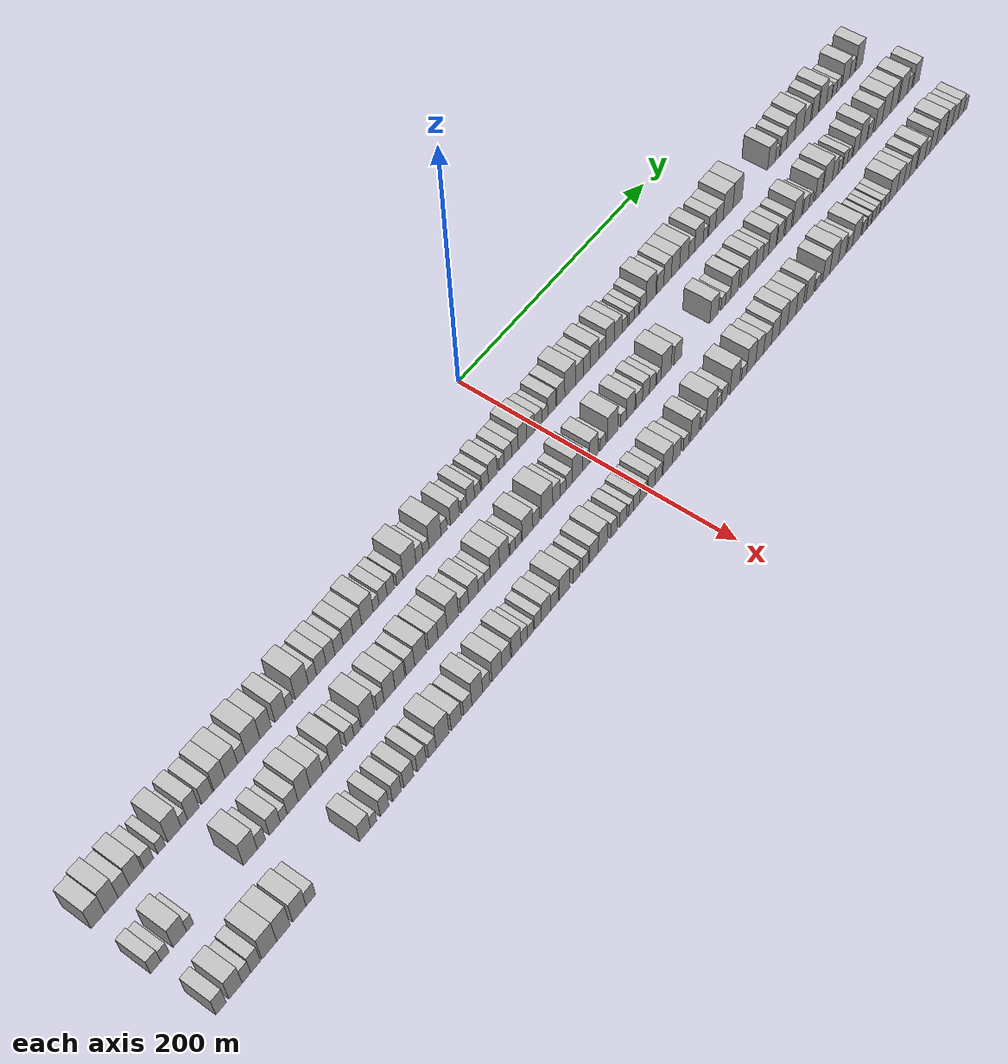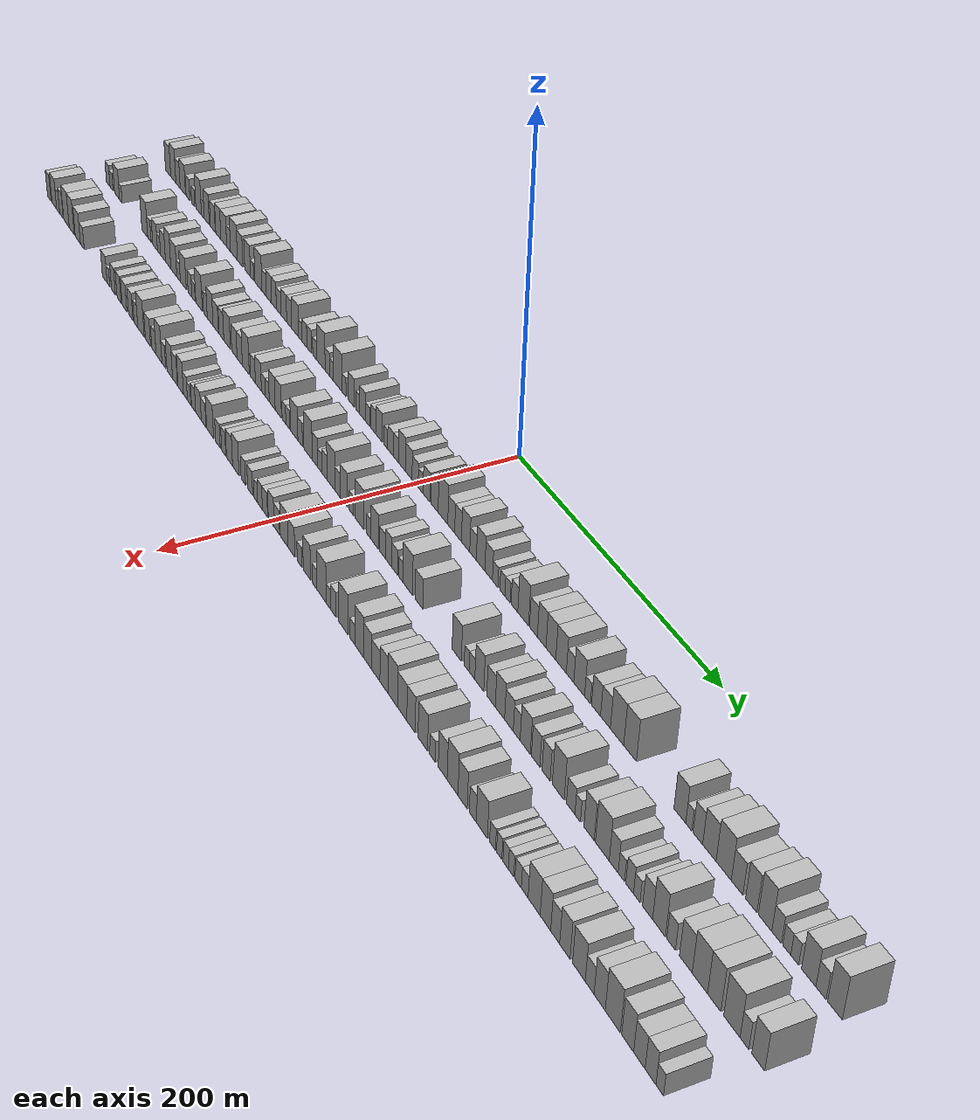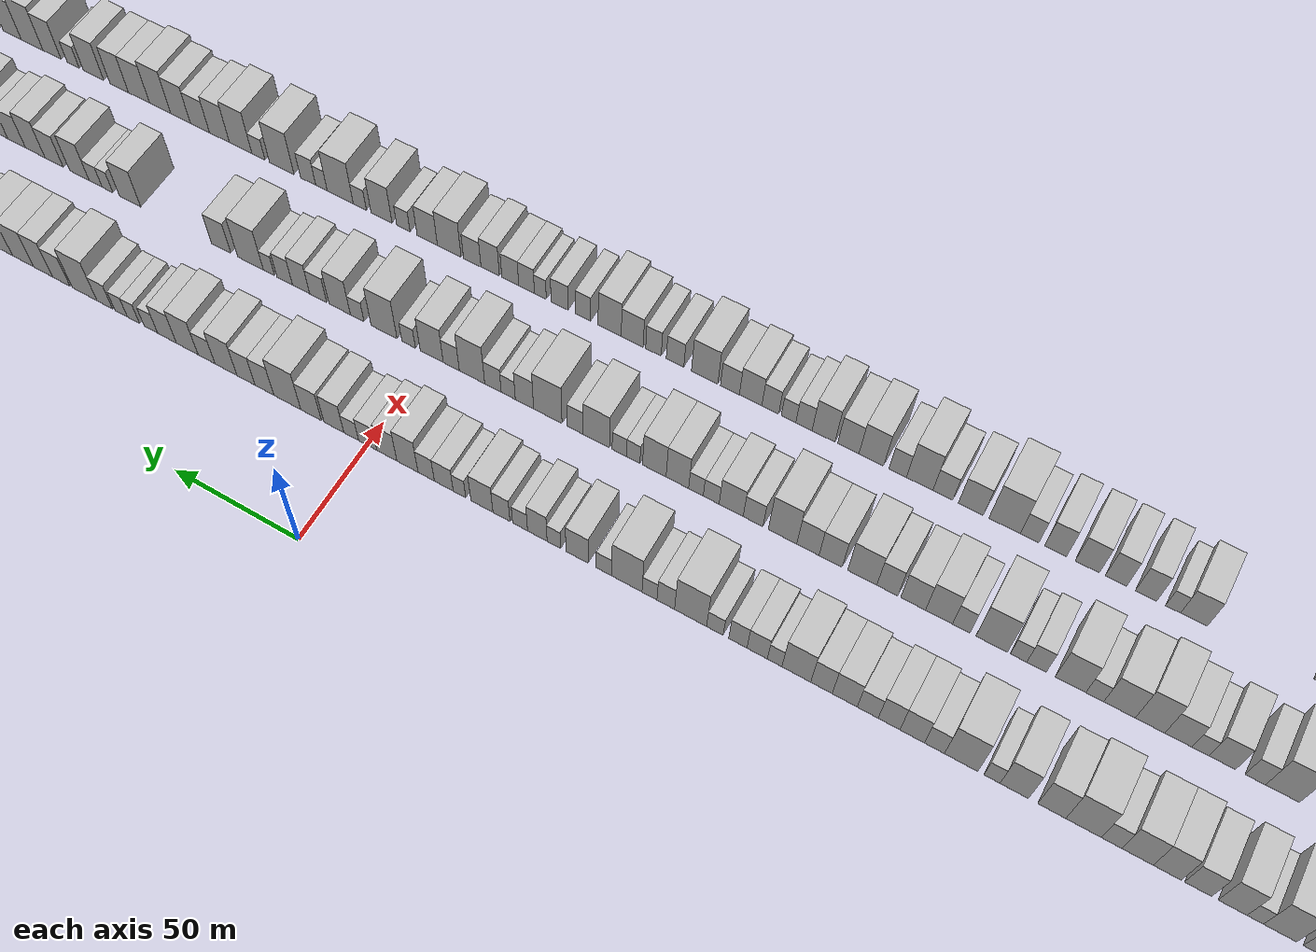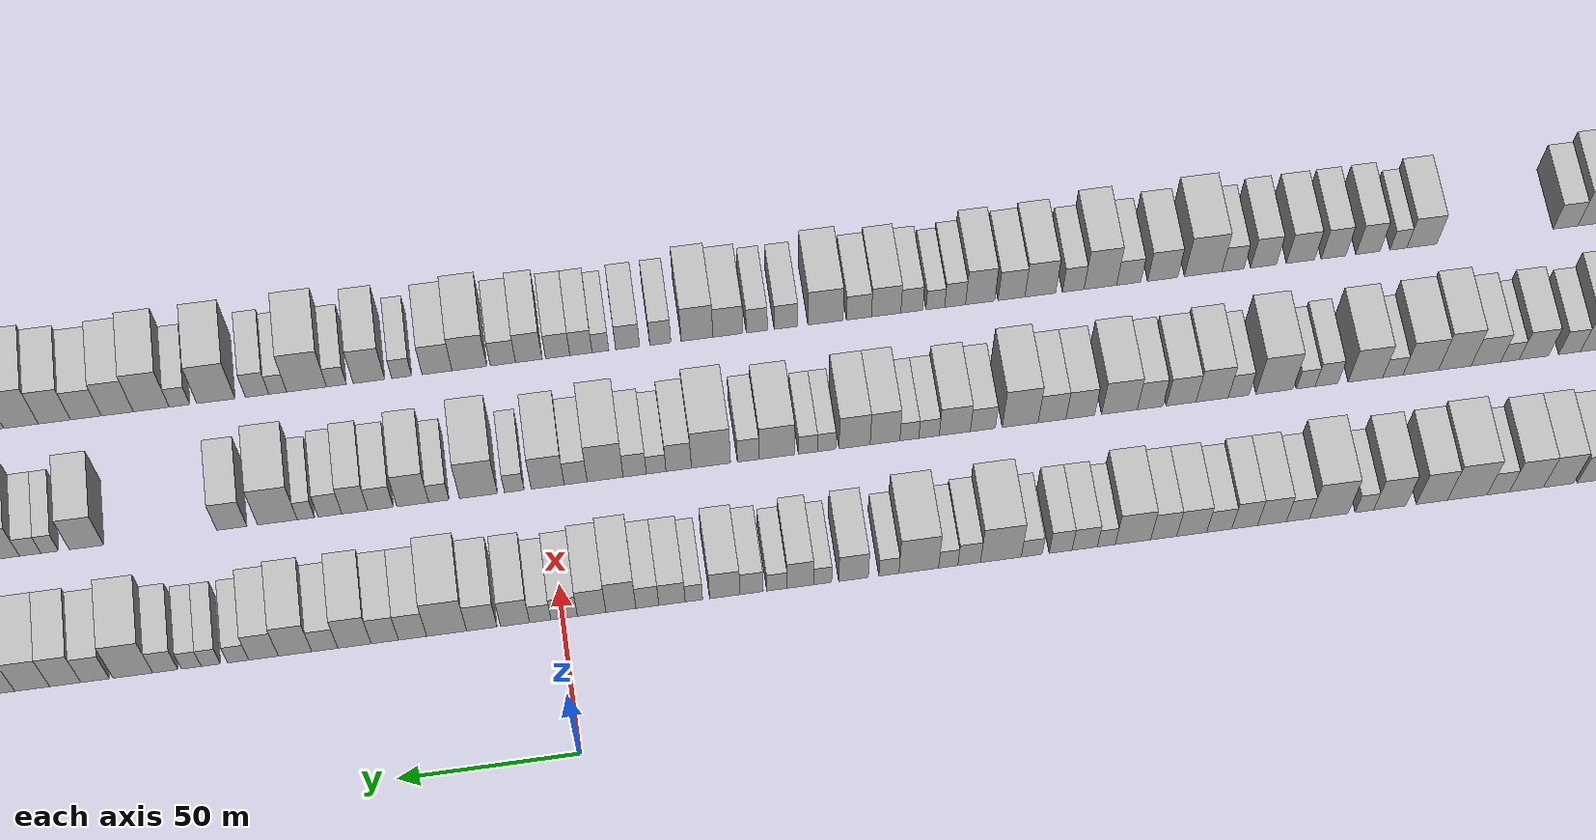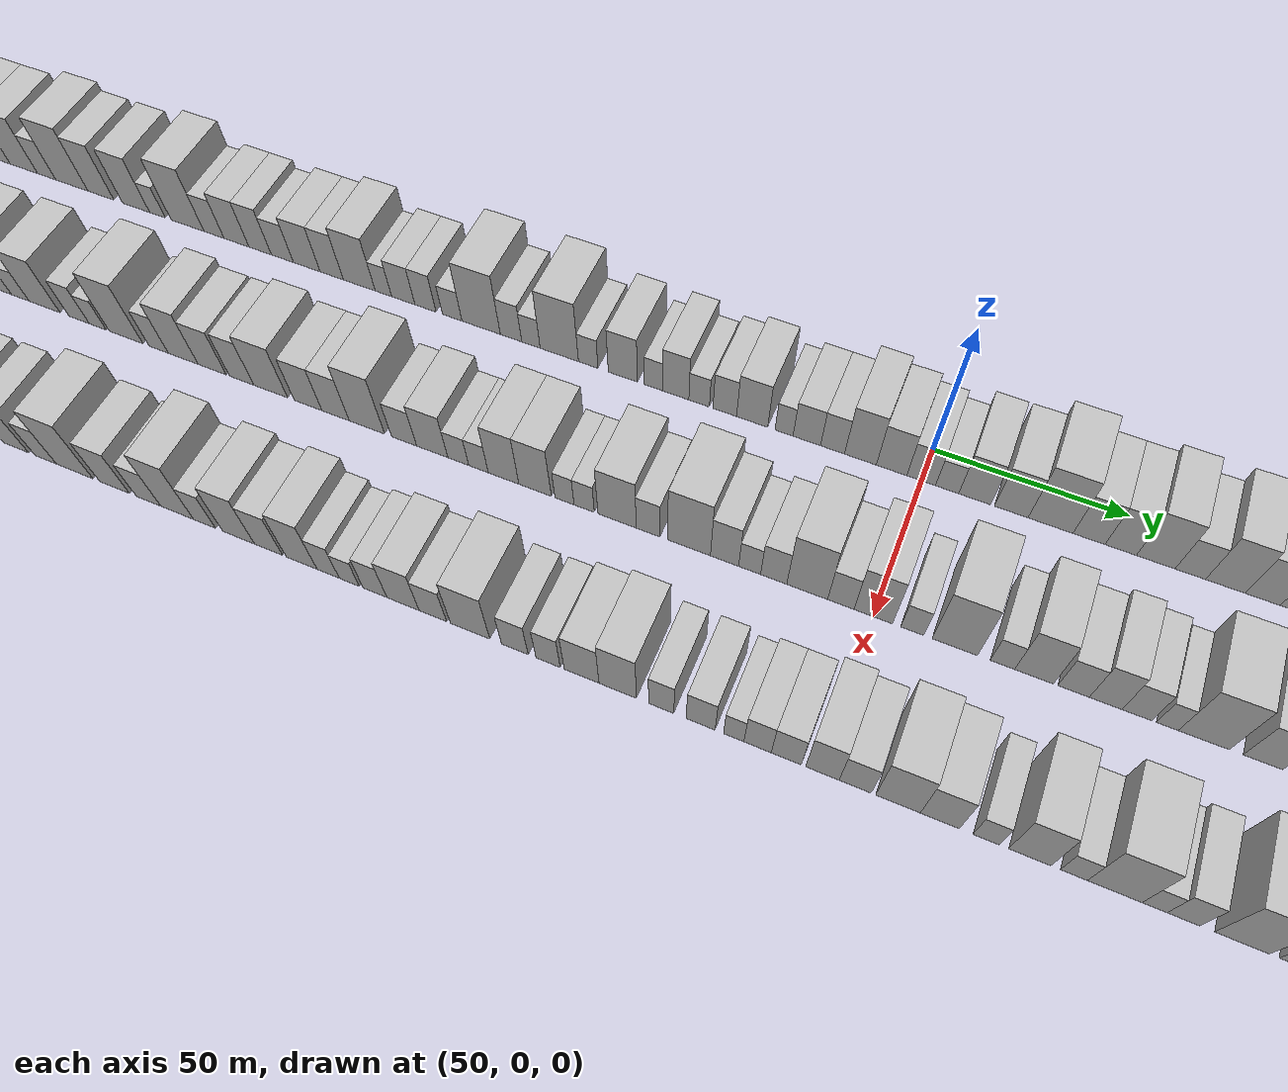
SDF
<sdf version="1.6">
 <world name="default">
  <scene>
   <sky><clouds><speed>12</speed></clouds></sky>
   <ambient>0.4 0.4 0.4 1</ambient>
   <background>0.7 0.7 0.7 1</background>
   <shadows>1</shadows>
  </scene>
  <gravity>0 0 -9.8066</gravity>
  <magnetic_field>6e-06 2.3e-05 -4.2e-05</magnetic_field>
  <physics default="0" name="default_physics" type="ode">
   <ode>
    <solver>
     <type>quick</type>
     <iters>10</iters>
     <sor>1.0</sor>
     <use_dynamic_moi_rescaling>0</use_dynamic_moi_rescaling>
    </solver>
    <constraints>
     <cfm>0</cfm>
     <erp>0.2</erp>
     <contact_max_correcting_vel>100</contact_max_correcting_vel>
     <contact_surface_layer>0.001</contact_surface_layer>
    </constraints>
   </ode>
   <max_step_size>0.004</max_step_size>
   <real_time_factor>1</real_time_factor>
   <real_time_update_rate>250</real_time_update_rate>
  </physics>
  <light name="sun" type="directional">
   <pose>0 0 10 0 0 0</pose>
   <diffuse>0.8 0.8 0.8 1</diffuse>
   <specular>0.2 0.2 0.2 1</specular>
   <attenuation>
    <range>1000</range>
    <constant>0.9</constant>
    <linear>0.01</linear>
    <quadratic>0.001</quadratic>
   </attenuation>
   <direction>-0.5 0.1 -0.9</direction>
  </light>
  <model name="building_1">
   <static>1</static>
   <pose>50.0000 -375.0617 0 0.000000 0.000000 0.000000</pose>
   <link name="link">
    <pose>0 0 10.50 0 0 0</pose>
    <collision name="collision"><geometry><box><size>20.0000 9.8766 21.0000</size></box></geometry></collision>
    <visual name="visual">
     <cast_shadows>0</cast_shadows>
     <geometry><box><size>20.0000 9.8766 21.0000</size></box></geometry>
     <material>
      <script>
       <uri>model://HANNAS_wall/materials/scripts</uri>
       <uri>model://HANNAS_wall/materials/textures</uri>
       <name>vrc/HANNAS_wall</name>
      </script>
     </material>
    </visual>
   </link>
  </model>
  <model name="building_2">
   <static>1</static>
   <pose>50.0000 -365.2726 0 0.000000 0.000000 0.000000</pose>
   <link name="link">
    <pose>0 0 12.00 0 0 0</pose>
    <collision name="collision"><geometry><box><size>20.0000 9.7016 24.0000</size></box></geometry></collision>
    <visual name="visual">
     <cast_shadows>0</cast_shadows>
     <geometry><box><size>20.0000 9.7016 24.0000</size></box></geometry>
     <material>
      <script>
       <uri>model://HANNAS_wall/materials/scripts</uri>
       <uri>model://HANNAS_wall/materials/textures</uri>
       <name>vrc/HANNAS_wall</name>
      </script>
     </material>
    </visual>
   </link>
  </model>
  <model name="building_3">
   <static>1</static>
   <pose>50.0000 -356.4059 0 0.000000 0.000000 0.000000</pose>
   <link name="link">
    <pose>0 0 9.00 0 0 0</pose>
    <collision name="collision"><geometry><box><size>20.0000 8.0318 18.0000</size></box></geometry></collision>
    <visual name="visual">
     <cast_shadows>0</cast_shadows>
     <geometry><box><size>20.0000 8.0318 18.0000</size></box></geometry>
     <material>
      <script>
       <uri>model://HANNAS_wall/materials/scripts</uri>
       <uri>model://HANNAS_wall/materials/textures</uri>
       <name>vrc/HANNAS_wall</name>
      </script>
     </material>
    </visual>
   </link>
  </model>
  <model name="building_4">
   <static>1</static>
   <pose>50.0000 -347.4172 0 0.000000 0.000000 0.000000</pose>
   <link name="link">
    <pose>0 0 10.50 0 0 0</pose>
    <collision name="collision"><geometry><box><size>20.0000 9.9455 21.0000</size></box></geometry></collision>
    <visual name="visual">
     <cast_shadows>0</cast_shadows>
     <geometry><box><size>20.0000 9.9455 21.0000</size></box></geometry>
     <material>
      <script>
       <uri>model://HANNAS_wall/materials/scripts</uri>
       <uri>model://HANNAS_wall/materials/textures</uri>
       <name>vrc/HANNAS_wall</name>
      </script>
     </material>
    </visual>
   </link>
  </model>
  <model name="building_5">
   <static>1</static>
   <pose>50.0000 -337.9303 0 0.000000 0.000000 0.000000</pose>
   <link name="link">
    <pose>0 0 7.50 0 0 0</pose>
    <collision name="collision"><geometry><box><size>20.0000 7.0283 15.0000</size></box></geometry></collision>
    <visual name="visual">
     <cast_shadows>0</cast_shadows>
     <geometry><box><size>20.0000 7.0283 15.0000</size></box></geometry>
     <material>
      <script>
       <uri>model://HANNAS_wall/materials/scripts</uri>
       <uri>model://HANNAS_wall/materials/textures</uri>
       <name>vrc/HANNAS_wall</name>
      </script>
     </material>
    </visual>
   </link>
  </model>
  <model name="building_6">
   <static>1</static>
   <pose>50.0000 -328.5971 0 0.000000 0.000000 0.000000</pose>
   <link name="link">
    <pose>0 0 6.00 0 0 0</pose>
    <collision name="collision"><geometry><box><size>20.0000 5.6383 12.0000</size></box></geometry></collision>
    <visual name="visual">
     <cast_shadows>0</cast_shadows>
     <geometry><box><size>20.0000 5.6383 12.0000</size></box></geometry>
     <material>
      <script>
       <uri>model://HANNAS_wall/materials/scripts</uri>
       <uri>model://HANNAS_wall/materials/textures</uri>
       <name>vrc/HANNAS_wall</name>
      </script>
     </material>
    </visual>
   </link>
  </model>
  <model name="building_7">
   <static>1</static>
   <pose>50.0000 -318.7597 0 0.000000 0.000000 0.000000</pose>
   <link name="link">
    <pose>0 0 12.00 0 0 0</pose>
    <collision name="collision"><geometry><box><size>20.0000 10.0365 24.0000</size></box></geometry></collision>
    <visual name="visual">
     <cast_shadows>0</cast_shadows>
     <geometry><box><size>20.0000 10.0365 24.0000</size></box></geometry>
     <material>
      <script>
       <uri>model://HANNAS_wall/materials/scripts</uri>
       <uri>model://HANNAS_wall/materials/textures</uri>
       <name>vrc/HANNAS_wall</name>
      </script>
     </material>
    </visual>
   </link>
  </model>
  <model name="building_8">
   <static>1</static>
   <pose>50.0000 -311.2489 0 0.000000 0.000000 0.000000</pose>
   <link name="link">
    <pose>0 0 6.00 0 0 0</pose>
    <collision name="collision"><geometry><box><size>20.0000 4.9851 12.0000</size></box></geometry></collision>
    <visual name="visual">
     <cast_shadows>0</cast_shadows>
     <geometry><box><size>20.0000 4.9851 12.0000</size></box></geometry>
     <material>
      <script>
       <uri>model://HANNAS_wall/materials/scripts</uri>
       <uri>model://HANNAS_wall/materials/textures</uri>
       <name>vrc/HANNAS_wall</name>
      </script>
     </material>
    </visual>
   </link>
  </model>
  <model name="building_9">
   <static>1</static>
   <pose>50.0000 -304.3338 0 0.000000 0.000000 0.000000</pose>
   <link name="link">
    <pose>0 0 10.50 0 0 0</pose>
    <collision name="collision"><geometry><box><size>20.0000 8.8450 21.0000</size></box></geometry></collision>
    <visual name="visual">
     <cast_shadows>0</cast_shadows>
     <geometry><box><size>20.0000 8.8450 21.0000</size></box></geometry>
     <material>
      <script>
       <uri>model://HANNAS_wall/materials/scripts</uri>
       <uri>model://HANNAS_wall/materials/textures</uri>
       <name>vrc/HANNAS_wall</name>
      </script>
     </material>
    </visual>
   </link>
  </model>
  <model name="building_10">
   <static>1</static>
   <pose>50.0000 -293.7215 0 0.000000 0.000000 0.000000</pose>
   <link name="link">
    <pose>0 0 9.00 0 0 0</pose>
    <collision name="collision"><geometry><box><size>20.0000 8.3798 18.0000</size></box></geometry></collision>
    <visual name="visual">
     <cast_shadows>0</cast_shadows>
     <geometry><box><size>20.0000 8.3798 18.0000</size></box></geometry>
     <material>
      <script>
       <uri>model://HANNAS_wall/materials/scripts</uri>
       <uri>model://HANNAS_wall/materials/textures</uri>
       <name>vrc/HANNAS_wall</name>
      </script>
     </material>
    </visual>
   </link>
  </model>
  <model name="building_11">
   <static>1</static>
   <pose>50.0000 -284.1320 0 0.000000 0.000000 0.000000</pose>
   <link name="link">
    <pose>0 0 10.50 0 0 0</pose>
    <collision name="collision"><geometry><box><size>20.0000 8.7991 21.0000</size></box></geometry></collision>
    <visual name="visual">
     <cast_shadows>0</cast_shadows>
     <geometry><box><size>20.0000 8.7991 21.0000</size></box></geometry>
     <material>
      <script>
       <uri>model://HANNAS_wall/materials/scripts</uri>
       <uri>model://HANNAS_wall/materials/textures</uri>
       <name>vrc/HANNAS_wall</name>
      </script>
     </material>
    </visual>
   </link>
  </model>
  <model name="building_12">
   <static>1</static>
   <pose>50.0000 -274.7714 0 0.000000 0.000000 0.000000</pose>
   <link name="link">
    <pose>0 0 10.50 0 0 0</pose>
    <collision name="collision"><geometry><box><size>20.0000 9.9222 21.0000</size></box></geometry></collision>
    <visual name="visual">
     <cast_shadows>0</cast_shadows>
     <geometry><box><size>20.0000 9.9222 21.0000</size></box></geometry>
     <material>
      <script>
       <uri>model://HANNAS_wall/materials/scripts</uri>
       <uri>model://HANNAS_wall/materials/textures</uri>
       <name>vrc/HANNAS_wall</name>
      </script>
     </material>
    </visual>
   </link>
  </model>
  <model name="building_13">
   <static>1</static>
   <pose>50.0000 -266.5715 0 0.000000 0.000000 0.000000</pose>
   <link name="link">
    <pose>0 0 7.50 0 0 0</pose>
    <collision name="collision"><geometry><box><size>20.0000 6.4775 15.0000</size></box></geometry></collision>
    <visual name="visual">
     <cast_shadows>0</cast_shadows>
     <geometry><box><size>20.0000 6.4775 15.0000</size></box></geometry>
     <material>
      <script>
       <uri>model://HANNAS_wall/materials/scripts</uri>
       <uri>model://HANNAS_wall/materials/textures</uri>
       <name>vrc/HANNAS_wall</name>
      </script>
     </material>
    </visual>
   </link>
  </model>
  <model name="building_14">
   <static>1</static>
   <pose>50.0000 -257.6300 0 0.000000 0.000000 0.000000</pose>
   <link name="link">
    <pose>0 0 12.00 0 0 0</pose>
    <collision name="collision"><geometry><box><size>20.0000 11.4055 24.0000</size></box></geometry></collision>
    <visual name="visual">
     <cast_shadows>0</cast_shadows>
     <geometry><box><size>20.0000 11.4055 24.0000</size></box></geometry>
     <material>
      <script>
       <uri>model://HANNAS_wall/materials/scripts</uri>
       <uri>model://HANNAS_wall/materials/textures</uri>
       <name>vrc/HANNAS_wall</name>
      </script>
     </material>
    </visual>
   </link>
  </model>
  <model name="building_15">
   <static>1</static>
   <pose>50.0000 -247.3824 0 0.000000 0.000000 0.000000</pose>
   <link name="link">
    <pose>0 0 10.50 0 0 0</pose>
    <collision name="collision"><geometry><box><size>20.0000 9.0897 21.0000</size></box></geometry></collision>
    <visual name="visual">
     <cast_shadows>0</cast_shadows>
     <geometry><box><size>20.0000 9.0897 21.0000</size></box></geometry>
     <material>
      <script>
       <uri>model://HANNAS_wall/materials/scripts</uri>
       <uri>model://HANNAS_wall/materials/textures</uri>
       <name>vrc/HANNAS_wall</name>
      </script>
     </material>
    </visual>
   </link>
  </model>
  <model name="building_16">
   <static>1</static>
   <pose>50.0000 -235.1703 0 0.000000 0.000000 0.000000</pose>
   <link name="link">
    <pose>0 0 10.50 0 0 0</pose>
    <collision name="collision"><geometry><box><size>20.0000 9.3346 21.0000</size></box></geometry></collision>
    <visual name="visual">
     <cast_shadows>0</cast_shadows>
     <geometry><box><size>20.0000 9.3346 21.0000</size></box></geometry>
     <material>
      <script>
       <uri>model://HANNAS_wall/materials/scripts</uri>
       <uri>model://HANNAS_wall/materials/textures</uri>
       <name>vrc/HANNAS_wall</name>
      </script>
     </material>
    </visual>
   </link>
  </model>
  <model name="building_17">
   <static>1</static>
   <pose>50.0000 -227.8410 0 0.000000 0.000000 0.000000</pose>
   <link name="link">
    <pose>0 0 6.00 0 0 0</pose>
    <collision name="collision"><geometry><box><size>20.0000 5.3239 12.0000</size></box></geometry></collision>
    <visual name="visual">
     <cast_shadows>0</cast_shadows>
     <geometry><box><size>20.0000 5.3239 12.0000</size></box></geometry>
     <material>
      <script>
       <uri>model://HANNAS_wall/materials/scripts</uri>
       <uri>model://HANNAS_wall/materials/textures</uri>
       <name>vrc/HANNAS_wall</name>
      </script>
     </material>
    </visual>
   </link>
  </model>
  <model name="building_18">
   <static>1</static>
   <pose>50.0000 -217.6135 0 0.000000 0.000000 0.000000</pose>
   <link name="link">
    <pose>0 0 12.00 0 0 0</pose>
    <collision name="collision"><geometry><box><size>20.0000 11.1311 24.0000</size></box></geometry></collision>
    <visual name="visual">
     <cast_shadows>0</cast_shadows>
     <geometry><box><size>20.0000 11.1311 24.0000</size></box></geometry>
     <material>
      <script>
       <uri>model://HANNAS_wall/materials/scripts</uri>
       <uri>model://HANNAS_wall/materials/textures</uri>
       <name>vrc/HANNAS_wall</name>
      </script>
     </material>
    </visual>
   </link>
  </model>
  <model name="building_19">
   <static>1</static>
   <pose>50.0000 -208.6832 0 0.000000 0.000000 0.000000</pose>
   <link name="link">
    <pose>0 0 7.50 0 0 0</pose>
    <collision name="collision"><geometry><box><size>20.0000 6.7295 15.0000</size></box></geometry></collision>
    <visual name="visual">
     <cast_shadows>0</cast_shadows>
     <geometry><box><size>20.0000 6.7295 15.0000</size></box></geometry>
     <material>
      <script>
       <uri>model://HANNAS_wall/materials/scripts</uri>
       <uri>model://HANNAS_wall/materials/textures</uri>
       <name>vrc/HANNAS_wall</name>
      </script>
     </material>
    </visual>
   </link>
  </model>
  <model name="building_20">
   <static>1</static>
   <pose>50.0000 -201.1800 0 0.000000 0.000000 0.000000</pose>
   <link name="link">
    <pose>0 0 9.00 0 0 0</pose>
    <collision name="collision"><geometry><box><size>20.0000 8.2770 18.0000</size></box></geometry></collision>
    <visual name="visual">
     <cast_shadows>0</cast_shadows>
     <geometry><box><size>20.0000 8.2770 18.0000</size></box></geometry>
     <material>
      <script>
       <uri>model://HANNAS_wall/materials/scripts</uri>
       <uri>model://HANNAS_wall/materials/textures</uri>
       <name>vrc/HANNAS_wall</name>
      </script>
     </material>
    </visual>
   </link>
  </model>
  <model name="building_21">
   <static>1</static>
   <pose>50.0000 -193.3477 0 0.000000 0.000000 0.000000</pose>
   <link name="link">
    <pose>0 0 9.00 0 0 0</pose>
    <collision name="collision"><geometry><box><size>20.0000 7.3875 18.0000</size></box></geometry></collision>
    <visual name="visual">
     <cast_shadows>0</cast_shadows>
     <geometry><box><size>20.0000 7.3875 18.0000</size></box></geometry>
     <material>
      <script>
       <uri>model://HANNAS_wall/materials/scripts</uri>
       <uri>model://HANNAS_wall/materials/textures</uri>
       <name>vrc/HANNAS_wall</name>
      </script>
     </material>
    </visual>
   </link>
  </model>
  <model name="building_22">
   <static>1</static>
   <pose>50.0000 -186.0562 0 0.000000 0.000000 0.000000</pose>
   <link name="link">
    <pose>0 0 7.50 0 0 0</pose>
    <collision name="collision"><geometry><box><size>20.0000 7.1954 15.0000</size></box></geometry></collision>
    <visual name="visual">
     <cast_shadows>0</cast_shadows>
     <geometry><box><size>20.0000 7.1954 15.0000</size></box></geometry>
     <material>
      <script>
       <uri>model://HANNAS_wall/materials/scripts</uri>
       <uri>model://HANNAS_wall/materials/textures</uri>
       <name>vrc/HANNAS_wall</name>
      </script>
     </material>
    </visual>
   </link>
  </model>
  <model name="building_23">
   <static>1</static>
   <pose>50.0000 -178.1469 0 0.000000 0.000000 0.000000</pose>
   <link name="link">
    <pose>0 0 9.00 0 0 0</pose>
    <collision name="collision"><geometry><box><size>20.0000 8.6233 18.0000</size></box></geometry></collision>
    <visual name="visual">
     <cast_shadows>0</cast_shadows>
     <geometry><box><size>20.0000 8.6233 18.0000</size></box></geometry>
     <material>
      <script>
       <uri>model://HANNAS_wall/materials/scripts</uri>
       <uri>model://HANNAS_wall/materials/textures</uri>
       <name>vrc/HANNAS_wall</name>
      </script>
     </material>
    </visual>
   </link>
  </model>
  <model name="building_24">
   <static>1</static>
   <pose>50.0000 -170.1049 0 0.000000 0.000000 0.000000</pose>
   <link name="link">
    <pose>0 0 9.00 0 0 0</pose>
    <collision name="collision"><geometry><box><size>20.0000 7.4606 18.0000</size></box></geometry></collision>
    <visual name="visual">
     <cast_shadows>0</cast_shadows>
     <geometry><box><size>20.0000 7.4606 18.0000</size></box></geometry>
     <material>
      <script>
       <uri>model://HANNAS_wall/materials/scripts</uri>
       <uri>model://HANNAS_wall/materials/textures</uri>
       <name>vrc/HANNAS_wall</name>
      </script>
     </material>
    </visual>
   </link>
  </model>
  <model name="building_25">
   <static>1</static>
   <pose>50.0000 -161.3190 0 0.000000 0.000000 0.000000</pose>
   <link name="link">
    <pose>0 0 10.50 0 0 0</pose>
    <collision name="collision"><geometry><box><size>20.0000 10.1112 21.0000</size></box></geometry></collision>
    <visual name="visual">
     <cast_shadows>0</cast_shadows>
     <geometry><box><size>20.0000 10.1112 21.0000</size></box></geometry>
     <material>
      <script>
       <uri>model://HANNAS_wall/materials/scripts</uri>
       <uri>model://HANNAS_wall/materials/textures</uri>
       <name>vrc/HANNAS_wall</name>
      </script>
     </material>
    </visual>
   </link>
  </model>
  <model name="building_26">
   <static>1</static>
   <pose>50.0000 -153.6916 0 0.000000 0.000000 0.000000</pose>
   <link name="link">
    <pose>0 0 6.00 0 0 0</pose>
    <collision name="collision"><geometry><box><size>20.0000 5.1437 12.0000</size></box></geometry></collision>
    <visual name="visual">
     <cast_shadows>0</cast_shadows>
     <geometry><box><size>20.0000 5.1437 12.0000</size></box></geometry>
     <material>
      <script>
       <uri>model://HANNAS_wall/materials/scripts</uri>
       <uri>model://HANNAS_wall/materials/textures</uri>
       <name>vrc/HANNAS_wall</name>
      </script>
     </material>
    </visual>
   </link>
  </model>
  <model name="building_27">
   <static>1</static>
   <pose>50.0000 -147.5010 0 0.000000 0.000000 0.000000</pose>
   <link name="link">
    <pose>0 0 7.50 0 0 0</pose>
    <collision name="collision"><geometry><box><size>20.0000 7.2375 15.0000</size></box></geometry></collision>
    <visual name="visual">
     <cast_shadows>0</cast_shadows>
     <geometry><box><size>20.0000 7.2375 15.0000</size></box></geometry>
     <material>
      <script>
       <uri>model://HANNAS_wall/materials/scripts</uri>
       <uri>model://HANNAS_wall/materials/textures</uri>
       <name>vrc/HANNAS_wall</name>
      </script>
     </material>
    </visual>
   </link>
  </model>
  <model name="building_28">
   <static>1</static>
   <pose>50.0000 -140.6211 0 0.000000 0.000000 0.000000</pose>
   <link name="link">
    <pose>0 0 7.50 0 0 0</pose>
    <collision name="collision"><geometry><box><size>20.0000 6.5223 15.0000</size></box></geometry></collision>
    <visual name="visual">
     <cast_shadows>0</cast_shadows>
     <geometry><box><size>20.0000 6.5223 15.0000</size></box></geometry>
     <material>
      <script>
       <uri>model://HANNAS_wall/materials/scripts</uri>
       <uri>model://HANNAS_wall/materials/textures</uri>
       <name>vrc/HANNAS_wall</name>
      </script>
     </material>
    </visual>
   </link>
  </model>
  <model name="building_29">
   <static>1</static>
   <pose>50.0000 -132.3837 0 0.000000 0.000000 0.000000</pose>
   <link name="link">
    <pose>0 0 6.00 0 0 0</pose>
    <collision name="collision"><geometry><box><size>20.0000 5.9525 12.0000</size></box></geometry></collision>
    <visual name="visual">
     <cast_shadows>0</cast_shadows>
     <geometry><box><size>20.0000 5.9525 12.0000</size></box></geometry>
     <material>
      <script>
       <uri>model://HANNAS_wall/materials/scripts</uri>
       <uri>model://HANNAS_wall/materials/textures</uri>
       <name>vrc/HANNAS_wall</name>
      </script>
     </material>
    </visual>
   </link>
  </model>
  <model name="building_30">
   <static>1</static>
   <pose>50.0000 -123.6012 0 0.000000 0.000000 0.000000</pose>
   <link name="link">
    <pose>0 0 12.00 0 0 0</pose>
    <collision name="collision"><geometry><box><size>20.0000 11.6125 24.0000</size></box></geometry></collision>
    <visual name="visual">
     <cast_shadows>0</cast_shadows>
     <geometry><box><size>20.0000 11.6125 24.0000</size></box></geometry>
     <material>
      <script>
       <uri>model://HANNAS_wall/materials/scripts</uri>
       <uri>model://HANNAS_wall/materials/textures</uri>
       <name>vrc/HANNAS_wall</name>
      </script>
     </material>
    </visual>
   </link>
  </model>
  <model name="building_31">
   <static>1</static>
   <pose>50.0000 -114.5825 0 0.000000 0.000000 0.000000</pose>
   <link name="link">
    <pose>0 0 7.50 0 0 0</pose>
    <collision name="collision"><geometry><box><size>20.0000 6.4248 15.0000</size></box></geometry></collision>
    <visual name="visual">
     <cast_shadows>0</cast_shadows>
     <geometry><box><size>20.0000 6.4248 15.0000</size></box></geometry>
     <material>
      <script>
       <uri>model://HANNAS_wall/materials/scripts</uri>
       <uri>model://HANNAS_wall/materials/textures</uri>
       <name>vrc/HANNAS_wall</name>
      </script>
     </material>
    </visual>
   </link>
  </model>
  <model name="building_32">
   <static>1</static>
   <pose>50.0000 -108.6283 0 0.000000 0.000000 0.000000</pose>
   <link name="link">
    <pose>0 0 6.00 0 0 0</pose>
    <collision name="collision"><geometry><box><size>20.0000 5.4836 12.0000</size></box></geometry></collision>
    <visual name="visual">
     <cast_shadows>0</cast_shadows>
     <geometry><box><size>20.0000 5.4836 12.0000</size></box></geometry>
     <material>
      <script>
       <uri>model://HANNAS_wall/materials/scripts</uri>
       <uri>model://HANNAS_wall/materials/textures</uri>
       <name>vrc/HANNAS_wall</name>
      </script>
     </material>
    </visual>
   </link>
  </model>
  <model name="building_33">
   <static>1</static>
   <pose>50.0000 -100.2538 0 0.000000 0.000000 0.000000</pose>
   <link name="link">
    <pose>0 0 12.00 0 0 0</pose>
    <collision name="collision"><geometry><box><size>20.0000 11.2654 24.0000</size></box></geometry></collision>
    <visual name="visual">
     <cast_shadows>0</cast_shadows>
     <geometry><box><size>20.0000 11.2654 24.0000</size></box></geometry>
     <material>
      <script>
       <uri>model://HANNAS_wall/materials/scripts</uri>
       <uri>model://HANNAS_wall/materials/textures</uri>
       <name>vrc/HANNAS_wall</name>
      </script>
     </material>
    </visual>
   </link>
  </model>
  <model name="building_34">
   <static>1</static>
   <pose>50.0000 -91.7787 0 0.000000 0.000000 0.000000</pose>
   <link name="link">
    <pose>0 0 6.00 0 0 0</pose>
    <collision name="collision"><geometry><box><size>20.0000 5.6847 12.0000</size></box></geometry></collision>
    <visual name="visual">
     <cast_shadows>0</cast_shadows>
     <geometry><box><size>20.0000 5.6847 12.0000</size></box></geometry>
     <material>
      <script>
       <uri>model://HANNAS_wall/materials/scripts</uri>
       <uri>model://HANNAS_wall/materials/textures</uri>
       <name>vrc/HANNAS_wall</name>
      </script>
     </material>
    </visual>
   </link>
  </model>
  <model name="building_35">
   <static>1</static>
   <pose>50.0000 -81.7509 0 0.000000 0.000000 0.000000</pose>
   <link name="link">
    <pose>0 0 9.00 0 0 0</pose>
    <collision name="collision"><geometry><box><size>20.0000 8.3708 18.0000</size></box></geometry></collision>
    <visual name="visual">
     <cast_shadows>0</cast_shadows>
     <geometry><box><size>20.0000 8.3708 18.0000</size></box></geometry>
     <material>
      <script>
       <uri>model://HANNAS_wall/materials/scripts</uri>
       <uri>model://HANNAS_wall/materials/textures</uri>
       <name>vrc/HANNAS_wall</name>
      </script>
     </material>
    </visual>
   </link>
  </model>
  <model name="building_36">
   <static>1</static>
   <pose>50.0000 -72.9915 0 0.000000 0.000000 0.000000</pose>
   <link name="link">
    <pose>0 0 6.00 0 0 0</pose>
    <collision name="collision"><geometry><box><size>20.0000 5.1481 12.0000</size></box></geometry></collision>
    <visual name="visual">
     <cast_shadows>0</cast_shadows>
     <geometry><box><size>20.0000 5.1481 12.0000</size></box></geometry>
     <material>
      <script>
       <uri>model://HANNAS_wall/materials/scripts</uri>
       <uri>model://HANNAS_wall/materials/textures</uri>
       <name>vrc/HANNAS_wall</name>
      </script>
     </material>
    </visual>
   </link>
  </model>
  <model name="building_37">
   <static>1</static>
   <pose>50.0000 -66.6965 0 0.000000 0.000000 0.000000</pose>
   <link name="link">
    <pose>0 0 9.00 0 0 0</pose>
    <collision name="collision"><geometry><box><size>20.0000 7.4419 18.0000</size></box></geometry></collision>
    <visual name="visual">
     <cast_shadows>0</cast_shadows>
     <geometry><box><size>20.0000 7.4419 18.0000</size></box></geometry>
     <material>
      <script>
       <uri>model://HANNAS_wall/materials/scripts</uri>
       <uri>model://HANNAS_wall/materials/textures</uri>
       <name>vrc/HANNAS_wall</name>
      </script>
     </material>
    </visual>
   </link>
  </model>
  <model name="building_38">
   <static>1</static>
   <pose>50.0000 -60.1013 0 0.000000 0.000000 0.000000</pose>
   <link name="link">
    <pose>0 0 6.00 0 0 0</pose>
    <collision name="collision"><geometry><box><size>20.0000 5.7485 12.0000</size></box></geometry></collision>
    <visual name="visual">
     <cast_shadows>0</cast_shadows>
     <geometry><box><size>20.0000 5.7485 12.0000</size></box></geometry>
     <material>
      <script>
       <uri>model://HANNAS_wall/materials/scripts</uri>
       <uri>model://HANNAS_wall/materials/textures</uri>
       <name>vrc/HANNAS_wall</name>
      </script>
     </material>
    </visual>
   </link>
  </model>
  <model name="building_39">
   <static>1</static>
   <pose>50.0000 -52.9512 0 0.000000 0.000000 0.000000</pose>
   <link name="link">
    <pose>0 0 7.50 0 0 0</pose>
    <collision name="collision"><geometry><box><size>20.0000 6.5517 15.0000</size></box></geometry></collision>
    <visual name="visual">
     <cast_shadows>0</cast_shadows>
     <geometry><box><size>20.0000 6.5517 15.0000</size></box></geometry>
     <material>
      <script>
       <uri>model://HANNAS_wall/materials/scripts</uri>
       <uri>model://HANNAS_wall/materials/textures</uri>
       <name>vrc/HANNAS_wall</name>
      </script>
     </material>
    </visual>
   </link>
  </model>
  <model name="building_40">
   <static>1</static>
   <pose>50.0000 -45.3979 0 0.000000 0.000000 0.000000</pose>
   <link name="link">
    <pose>0 0 9.00 0 0 0</pose>
    <collision name="collision"><geometry><box><size>20.0000 8.5549 18.0000</size></box></geometry></collision>
    <visual name="visual">
     <cast_shadows>0</cast_shadows>
     <geometry><box><size>20.0000 8.5549 18.0000</size></box></geometry>
     <material>
      <script>
       <uri>model://HANNAS_wall/materials/scripts</uri>
       <uri>model://HANNAS_wall/materials/textures</uri>
       <name>vrc/HANNAS_wall</name>
      </script>
     </material>
    </visual>
   </link>
  </model>
  <model name="building_41">
   <static>1</static>
   <pose>50.0000 -36.6733 0 0.000000 0.000000 0.000000</pose>
   <link name="link">
    <pose>0 0 6.00 0 0 0</pose>
    <collision name="collision"><geometry><box><size>20.0000 4.8943 12.0000</size></box></geometry></collision>
    <visual name="visual">
     <cast_shadows>0</cast_shadows>
     <geometry><box><size>20.0000 4.8943 12.0000</size></box></geometry>
     <material>
      <script>
       <uri>model://HANNAS_wall/materials/scripts</uri>
       <uri>model://HANNAS_wall/materials/textures</uri>
       <name>vrc/HANNAS_wall</name>
      </script>
     </material>
    </visual>
   </link>
  </model>
  <model name="building_42">
   <static>1</static>
   <pose>50.0000 -30.5154 0 0.000000 0.000000 0.000000</pose>
   <link name="link">
    <pose>0 0 7.50 0 0 0</pose>
    <collision name="collision"><geometry><box><size>20.0000 7.4215 15.0000</size></box></geometry></collision>
    <visual name="visual">
     <cast_shadows>0</cast_shadows>
     <geometry><box><size>20.0000 7.4215 15.0000</size></box></geometry>
     <material>
      <script>
       <uri>model://HANNAS_wall/materials/scripts</uri>
       <uri>model://HANNAS_wall/materials/textures</uri>
       <name>vrc/HANNAS_wall</name>
      </script>
     </material>
    </visual>
   </link>
  </model>
  <model name="building_43">
   <static>1</static>
   <pose>50.0000 -23.5866 0 0.000000 0.000000 0.000000</pose>
   <link name="link">
    <pose>0 0 7.50 0 0 0</pose>
    <collision name="collision"><geometry><box><size>20.0000 6.4360 15.0000</size></box></geometry></collision>
    <visual name="visual">
     <cast_shadows>0</cast_shadows>
     <geometry><box><size>20.0000 6.4360 15.0000</size></box></geometry>
     <material>
      <script>
       <uri>model://HANNAS_wall/materials/scripts</uri>
       <uri>model://HANNAS_wall/materials/textures</uri>
       <name>vrc/HANNAS_wall</name>
      </script>
     </material>
    </visual>
   </link>
  </model>
  <model name="building_44">
   <static>1</static>
   <pose>50.0000 -16.1588 0 0.000000 0.000000 0.000000</pose>
   <link name="link">
    <pose>0 0 10.50 0 0 0</pose>
    <collision name="collision"><geometry><box><size>20.0000 8.4197 21.0000</size></box></geometry></collision>
    <visual name="visual">
     <cast_shadows>0</cast_shadows>
     <geometry><box><size>20.0000 8.4197 21.0000</size></box></geometry>
     <material>
      <script>
       <uri>model://HANNAS_wall/materials/scripts</uri>
       <uri>model://HANNAS_wall/materials/textures</uri>
       <name>vrc/HANNAS_wall</name>
      </script>
     </material>
    </visual>
   </link>
  </model>
  <model name="building_45">
   <static>1</static>
   <pose>50.0000 -7.9561 0 0.000000 0.000000 0.000000</pose>
   <link name="link">
    <pose>0 0 9.00 0 0 0</pose>
    <collision name="collision"><geometry><box><size>20.0000 7.9856 18.0000</size></box></geometry></collision>
    <visual name="visual">
     <cast_shadows>0</cast_shadows>
     <geometry><box><size>20.0000 7.9856 18.0000</size></box></geometry>
     <material>
      <script>
       <uri>model://HANNAS_wall/materials/scripts</uri>
       <uri>model://HANNAS_wall/materials/textures</uri>
       <name>vrc/HANNAS_wall</name>
      </script>
     </material>
    </visual>
   </link>
  </model>
  <model name="building_46">
   <static>1</static>
   <pose>50.0000 -0.2505 0 0.000000 0.000000 0.000000</pose>
   <link name="link">
    <pose>0 0 7.50 0 0 0</pose>
    <collision name="collision"><geometry><box><size>20.0000 7.4255 15.0000</size></box></geometry></collision>
    <visual name="visual">
     <cast_shadows>0</cast_shadows>
     <geometry><box><size>20.0000 7.4255 15.0000</size></box></geometry>
     <material>
      <script>
       <uri>model://HANNAS_wall/materials/scripts</uri>
       <uri>model://HANNAS_wall/materials/textures</uri>
       <name>vrc/HANNAS_wall</name>
      </script>
     </material>
    </visual>
   </link>
  </model>
  <model name="building_47">
   <static>1</static>
   <pose>50.0000 6.4486 0 0.000000 0.000000 0.000000</pose>
   <link name="link">
    <pose>0 0 6.00 0 0 0</pose>
    <collision name="collision"><geometry><box><size>20.0000 5.9728 12.0000</size></box></geometry></collision>
    <visual name="visual">
     <cast_shadows>0</cast_shadows>
     <geometry><box><size>20.0000 5.9728 12.0000</size></box></geometry>
     <material>
      <script>
       <uri>model://HANNAS_wall/materials/scripts</uri>
       <uri>model://HANNAS_wall/materials/textures</uri>
       <name>vrc/HANNAS_wall</name>
      </script>
     </material>
    </visual>
   </link>
  </model>
  <model name="building_48">
   <static>1</static>
   <pose>50.0000 13.4981 0 0.000000 0.000000 0.000000</pose>
   <link name="link">
    <pose>0 0 9.00 0 0 0</pose>
    <collision name="collision"><geometry><box><size>20.0000 8.1262 18.0000</size></box></geometry></collision>
    <visual name="visual">
     <cast_shadows>0</cast_shadows>
     <geometry><box><size>20.0000 8.1262 18.0000</size></box></geometry>
     <material>
      <script>
       <uri>model://HANNAS_wall/materials/scripts</uri>
       <uri>model://HANNAS_wall/materials/textures</uri>
       <name>vrc/HANNAS_wall</name>
      </script>
     </material>
    </visual>
   </link>
  </model>
  <model name="building_49">
   <static>1</static>
   <pose>50.0000 22.7994 0 0.000000 0.000000 0.000000</pose>
   <link name="link">
    <pose>0 0 9.00 0 0 0</pose>
    <collision name="collision"><geometry><box><size>20.0000 8.4763 18.0000</size></box></geometry></collision>
    <visual name="visual">
     <cast_shadows>0</cast_shadows>
     <geometry><box><size>20.0000 8.4763 18.0000</size></box></geometry>
     <material>
      <script>
       <uri>model://HANNAS_wall/materials/scripts</uri>
       <uri>model://HANNAS_wall/materials/textures</uri>
       <name>vrc/HANNAS_wall</name>
      </script>
     </material>
    </visual>
   </link>
  </model>
  <model name="building_50">
   <static>1</static>
   <pose>50.0000 32.6208 0 0.000000 0.000000 0.000000</pose>
   <link name="link">
    <pose>0 0 12.00 0 0 0</pose>
    <collision name="collision"><geometry><box><size>20.0000 11.1666 24.0000</size></box></geometry></collision>
    <visual name="visual">
     <cast_shadows>0</cast_shadows>
     <geometry><box><size>20.0000 11.1666 24.0000</size></box></geometry>
     <material>
      <script>
       <uri>model://HANNAS_wall/materials/scripts</uri>
       <uri>model://HANNAS_wall/materials/textures</uri>
       <name>vrc/HANNAS_wall</name>
      </script>
     </material>
    </visual>
   </link>
  </model>
  <model name="building_51">
   <static>1</static>
   <pose>50.0000 42.1323 0 0.000000 0.000000 0.000000</pose>
   <link name="link">
    <pose>0 0 9.00 0 0 0</pose>
    <collision name="collision"><geometry><box><size>20.0000 7.8563 18.0000</size></box></geometry></collision>
    <visual name="visual">
     <cast_shadows>0</cast_shadows>
     <geometry><box><size>20.0000 7.8563 18.0000</size></box></geometry>
     <material>
      <script>
       <uri>model://HANNAS_wall/materials/scripts</uri>
       <uri>model://HANNAS_wall/materials/textures</uri>
       <name>vrc/HANNAS_wall</name>
      </script>
     </material>
    </visual>
   </link>
  </model>
  <model name="building_52">
   <static>1</static>
   <pose>50.0000 49.8642 0 0.000000 0.000000 0.000000</pose>
   <link name="link">
    <pose>0 0 9.00 0 0 0</pose>
    <collision name="collision"><geometry><box><size>20.0000 7.6075 18.0000</size></box></geometry></collision>
    <visual name="visual">
     <cast_shadows>0</cast_shadows>
     <geometry><box><size>20.0000 7.6075 18.0000</size></box></geometry>
     <material>
      <script>
       <uri>model://HANNAS_wall/materials/scripts</uri>
       <uri>model://HANNAS_wall/materials/textures</uri>
       <name>vrc/HANNAS_wall</name>
      </script>
     </material>
    </visual>
   </link>
  </model>
  <model name="building_53">
   <static>1</static>
   <pose>50.0000 58.3111 0 0.000000 0.000000 0.000000</pose>
   <link name="link">
    <pose>0 0 10.50 0 0 0</pose>
    <collision name="collision"><geometry><box><size>20.0000 9.2863 21.0000</size></box></geometry></collision>
    <visual name="visual">
     <cast_shadows>0</cast_shadows>
     <geometry><box><size>20.0000 9.2863 21.0000</size></box></geometry>
     <material>
      <script>
       <uri>model://HANNAS_wall/materials/scripts</uri>
       <uri>model://HANNAS_wall/materials/textures</uri>
       <name>vrc/HANNAS_wall</name>
      </script>
     </material>
    </visual>
   </link>
  </model>
  <model name="building_54">
   <static>1</static>
   <pose>50.0000 66.5631 0 0.000000 0.000000 0.000000</pose>
   <link name="link">
    <pose>0 0 7.50 0 0 0</pose>
    <collision name="collision"><geometry><box><size>20.0000 7.2175 15.0000</size></box></geometry></collision>
    <visual name="visual">
     <cast_shadows>0</cast_shadows>
     <geometry><box><size>20.0000 7.2175 15.0000</size></box></geometry>
     <material>
      <script>
       <uri>model://HANNAS_wall/materials/scripts</uri>
       <uri>model://HANNAS_wall/materials/textures</uri>
       <name>vrc/HANNAS_wall</name>
      </script>
     </material>
    </visual>
   </link>
  </model>
  <model name="building_55">
   <static>1</static>
   <pose>50.0000 74.8144 0 0.000000 0.000000 0.000000</pose>
   <link name="link">
    <pose>0 0 10.50 0 0 0</pose>
    <collision name="collision"><geometry><box><size>20.0000 9.2851 21.0000</size></box></geometry></collision>
    <visual name="visual">
     <cast_shadows>0</cast_shadows>
     <geometry><box><size>20.0000 9.2851 21.0000</size></box></geometry>
     <material>
      <script>
       <uri>model://HANNAS_wall/materials/scripts</uri>
       <uri>model://HANNAS_wall/materials/textures</uri>
       <name>vrc/HANNAS_wall</name>
      </script>
     </material>
    </visual>
   </link>
  </model>
  <model name="building_56">
   <static>1</static>
   <pose>50.0000 83.5508 0 0.000000 0.000000 0.000000</pose>
   <link name="link">
    <pose>0 0 9.00 0 0 0</pose>
    <collision name="collision"><geometry><box><size>20.0000 8.1877 18.0000</size></box></geometry></collision>
    <visual name="visual">
     <cast_shadows>0</cast_shadows>
     <geometry><box><size>20.0000 8.1877 18.0000</size></box></geometry>
     <material>
      <script>
       <uri>model://HANNAS_wall/materials/scripts</uri>
       <uri>model://HANNAS_wall/materials/textures</uri>
       <name>vrc/HANNAS_wall</name>
      </script>
     </material>
    </visual>
   </link>
  </model>
  <model name="building_57">
   <static>1</static>
   <pose>50.0000 90.5819 0 0.000000 0.000000 0.000000</pose>
   <link name="link">
    <pose>0 0 6.00 0 0 0</pose>
    <collision name="collision"><geometry><box><size>20.0000 5.8745 12.0000</size></box></geometry></collision>
    <visual name="visual">
     <cast_shadows>0</cast_shadows>
     <geometry><box><size>20.0000 5.8745 12.0000</size></box></geometry>
     <material>
      <script>
       <uri>model://HANNAS_wall/materials/scripts</uri>
       <uri>model://HANNAS_wall/materials/textures</uri>
       <name>vrc/HANNAS_wall</name>
      </script>
     </material>
    </visual>
   </link>
  </model>
  <model name="building_58">
   <static>1</static>
   <pose>50.0000 98.1735 0 0.000000 0.000000 0.000000</pose>
   <link name="link">
    <pose>0 0 6.00 0 0 0</pose>
    <collision name="collision"><geometry><box><size>20.0000 5.3087 12.0000</size></box></geometry></collision>
    <visual name="visual">
     <cast_shadows>0</cast_shadows>
     <geometry><box><size>20.0000 5.3087 12.0000</size></box></geometry>
     <material>
      <script>
       <uri>model://HANNAS_wall/materials/scripts</uri>
       <uri>model://HANNAS_wall/materials/textures</uri>
       <name>vrc/HANNAS_wall</name>
      </script>
     </material>
    </visual>
   </link>
  </model>
  <model name="building_59">
   <static>1</static>
   <pose>50.0000 103.5518 0 0.000000 0.000000 0.000000</pose>
   <link name="link">
    <pose>0 0 6.00 0 0 0</pose>
    <collision name="collision"><geometry><box><size>20.0000 5.4480 12.0000</size></box></geometry></collision>
    <visual name="visual">
     <cast_shadows>0</cast_shadows>
     <geometry><box><size>20.0000 5.4480 12.0000</size></box></geometry>
     <material>
      <script>
       <uri>model://HANNAS_wall/materials/scripts</uri>
       <uri>model://HANNAS_wall/materials/textures</uri>
       <name>vrc/HANNAS_wall</name>
      </script>
     </material>
    </visual>
   </link>
  </model>
  <model name="building_60">
   <static>1</static>
   <pose>50.0000 110.7462 0 0.000000 0.000000 0.000000</pose>
   <link name="link">
    <pose>0 0 7.50 0 0 0</pose>
    <collision name="collision"><geometry><box><size>20.0000 6.9409 15.0000</size></box></geometry></collision>
    <visual name="visual">
     <cast_shadows>0</cast_shadows>
     <geometry><box><size>20.0000 6.9409 15.0000</size></box></geometry>
     <material>
      <script>
       <uri>model://HANNAS_wall/materials/scripts</uri>
       <uri>model://HANNAS_wall/materials/textures</uri>
       <name>vrc/HANNAS_wall</name>
      </script>
     </material>
    </visual>
   </link>
  </model>
  <model name="building_61">
   <static>1</static>
   <pose>50.0000 119.6971 0 0.000000 0.000000 0.000000</pose>
   <link name="link">
    <pose>0 0 12.00 0 0 0</pose>
    <collision name="collision"><geometry><box><size>20.0000 10.9610 24.0000</size></box></geometry></collision>
    <visual name="visual">
     <cast_shadows>0</cast_shadows>
     <geometry><box><size>20.0000 10.9610 24.0000</size></box></geometry>
     <material>
      <script>
       <uri>model://HANNAS_wall/materials/scripts</uri>
       <uri>model://HANNAS_wall/materials/textures</uri>
       <name>vrc/HANNAS_wall</name>
      </script>
     </material>
    </visual>
   </link>
  </model>
  <model name="building_62">
   <static>1</static>
   <pose>50.0000 130.1104 0 0.000000 0.000000 0.000000</pose>
   <link name="link">
    <pose>0 0 9.00 0 0 0</pose>
    <collision name="collision"><geometry><box><size>20.0000 7.8656 18.0000</size></box></geometry></collision>
    <visual name="visual">
     <cast_shadows>0</cast_shadows>
     <geometry><box><size>20.0000 7.8656 18.0000</size></box></geometry>
     <material>
      <script>
       <uri>model://HANNAS_wall/materials/scripts</uri>
       <uri>model://HANNAS_wall/materials/textures</uri>
       <name>vrc/HANNAS_wall</name>
      </script>
     </material>
    </visual>
   </link>
  </model>
  <model name="building_63">
   <static>1</static>
   <pose>50.0000 138.3364 0 0.000000 0.000000 0.000000</pose>
   <link name="link">
    <pose>0 0 10.50 0 0 0</pose>
    <collision name="collision"><geometry><box><size>20.0000 8.5863 21.0000</size></box></geometry></collision>
    <visual name="visual">
     <cast_shadows>0</cast_shadows>
     <geometry><box><size>20.0000 8.5863 21.0000</size></box></geometry>
     <material>
      <script>
       <uri>model://HANNAS_wall/materials/scripts</uri>
       <uri>model://HANNAS_wall/materials/textures</uri>
       <name>vrc/HANNAS_wall</name>
      </script>
     </material>
    </visual>
   </link>
  </model>
  <model name="building_64">
   <static>1</static>
   <pose>50.0000 147.4133 0 0.000000 0.000000 0.000000</pose>
   <link name="link">
    <pose>0 0 10.50 0 0 0</pose>
    <collision name="collision"><geometry><box><size>20.0000 9.5676 21.0000</size></box></geometry></collision>
    <visual name="visual">
     <cast_shadows>0</cast_shadows>
     <geometry><box><size>20.0000 9.5676 21.0000</size></box></geometry>
     <material>
      <script>
       <uri>model://HANNAS_wall/materials/scripts</uri>
       <uri>model://HANNAS_wall/materials/textures</uri>
       <name>vrc/HANNAS_wall</name>
      </script>
     </material>
    </visual>
   </link>
  </model>
  <model name="building_65">
   <static>1</static>
   <pose>50.0000 157.2730 0 0.000000 0.000000 0.000000</pose>
   <link name="link">
    <pose>0 0 10.50 0 0 0</pose>
    <collision name="collision"><geometry><box><size>20.0000 10.1517 21.0000</size></box></geometry></collision>
    <visual name="visual">
     <cast_shadows>0</cast_shadows>
     <geometry><box><size>20.0000 10.1517 21.0000</size></box></geometry>
     <material>
      <script>
       <uri>model://HANNAS_wall/materials/scripts</uri>
       <uri>model://HANNAS_wall/materials/textures</uri>
       <name>vrc/HANNAS_wall</name>
      </script>
     </material>
    </visual>
   </link>
  </model>
  <model name="building_66">
   <static>1</static>
   <pose>50.0000 165.8847 0 0.000000 0.000000 0.000000</pose>
   <link name="link">
    <pose>0 0 7.50 0 0 0</pose>
    <collision name="collision"><geometry><box><size>20.0000 7.0718 15.0000</size></box></geometry></collision>
    <visual name="visual">
     <cast_shadows>0</cast_shadows>
     <geometry><box><size>20.0000 7.0718 15.0000</size></box></geometry>
     <material>
      <script>
       <uri>model://HANNAS_wall/materials/scripts</uri>
       <uri>model://HANNAS_wall/materials/textures</uri>
       <name>vrc/HANNAS_wall</name>
      </script>
     </material>
    </visual>
   </link>
  </model>
  <model name="building_67">
   <static>1</static>
   <pose>50.0000 174.5126 0 0.000000 0.000000 0.000000</pose>
   <link name="link">
    <pose>0 0 10.50 0 0 0</pose>
    <collision name="collision"><geometry><box><size>20.0000 10.1839 21.0000</size></box></geometry></collision>
    <visual name="visual">
     <cast_shadows>0</cast_shadows>
     <geometry><box><size>20.0000 10.1839 21.0000</size></box></geometry>
     <material>
      <script>
       <uri>model://HANNAS_wall/materials/scripts</uri>
       <uri>model://HANNAS_wall/materials/textures</uri>
       <name>vrc/HANNAS_wall</name>
      </script>
     </material>
    </visual>
   </link>
  </model>
  <model name="building_68">
   <static>1</static>
   <pose>50.0000 182.3179 0 0.000000 0.000000 0.000000</pose>
   <link name="link">
    <pose>0 0 6.00 0 0 0</pose>
    <collision name="collision"><geometry><box><size>20.0000 5.4267 12.0000</size></box></geometry></collision>
    <visual name="visual">
     <cast_shadows>0</cast_shadows>
     <geometry><box><size>20.0000 5.4267 12.0000</size></box></geometry>
     <material>
      <script>
       <uri>model://HANNAS_wall/materials/scripts</uri>
       <uri>model://HANNAS_wall/materials/textures</uri>
       <name>vrc/HANNAS_wall</name>
      </script>
     </material>
    </visual>
   </link>
  </model>
  <model name="building_69">
   <static>1</static>
   <pose>50.0000 190.1722 0 0.000000 0.000000 0.000000</pose>
   <link name="link">
    <pose>0 0 9.00 0 0 0</pose>
    <collision name="collision"><geometry><box><size>20.0000 8.2820 18.0000</size></box></geometry></collision>
    <visual name="visual">
     <cast_shadows>0</cast_shadows>
     <geometry><box><size>20.0000 8.2820 18.0000</size></box></geometry>
     <material>
      <script>
       <uri>model://HANNAS_wall/materials/scripts</uri>
       <uri>model://HANNAS_wall/materials/textures</uri>
       <name>vrc/HANNAS_wall</name>
      </script>
     </material>
    </visual>
   </link>
  </model>
  <model name="building_70">
   <static>1</static>
   <pose>50.0000 198.7415 0 0.000000 0.000000 0.000000</pose>
   <link name="link">
    <pose>0 0 9.00 0 0 0</pose>
    <collision name="collision"><geometry><box><size>20.0000 8.8567 18.0000</size></box></geometry></collision>
    <visual name="visual">
     <cast_shadows>0</cast_shadows>
     <geometry><box><size>20.0000 8.8567 18.0000</size></box></geometry>
     <material>
      <script>
       <uri>model://HANNAS_wall/materials/scripts</uri>
       <uri>model://HANNAS_wall/materials/textures</uri>
       <name>vrc/HANNAS_wall</name>
      </script>
     </material>
    </visual>
   </link>
  </model>
  <model name="building_71">
   <static>1</static>
   <pose>50.0000 209.1260 0 0.000000 0.000000 0.000000</pose>
   <link name="link">
    <pose>0 0 12.00 0 0 0</pose>
    <collision name="collision"><geometry><box><size>20.0000 11.9123 24.0000</size></box></geometry></collision>
    <visual name="visual">
     <cast_shadows>0</cast_shadows>
     <geometry><box><size>20.0000 11.9123 24.0000</size></box></geometry>
     <material>
      <script>
       <uri>model://HANNAS_wall/materials/scripts</uri>
       <uri>model://HANNAS_wall/materials/textures</uri>
       <name>vrc/HANNAS_wall</name>
      </script>
     </material>
    </visual>
   </link>
  </model>
  <model name="building_72">
   <static>1</static>
   <pose>50.0000 220.6536 0 0.000000 0.000000 0.000000</pose>
   <link name="link">
    <pose>0 0 12.00 0 0 0</pose>
    <collision name="collision"><geometry><box><size>20.0000 11.1428 24.0000</size></box></geometry></collision>
    <visual name="visual">
     <cast_shadows>0</cast_shadows>
     <geometry><box><size>20.0000 11.1428 24.0000</size></box></geometry>
     <material>
      <script>
       <uri>model://HANNAS_wall/materials/scripts</uri>
       <uri>model://HANNAS_wall/materials/textures</uri>
       <name>vrc/HANNAS_wall</name>
      </script>
     </material>
    </visual>
   </link>
  </model>
  <model name="building_73">
   <static>1</static>
   <pose>50.0000 262.5950 0 0.000000 0.000000 0.000000</pose>
   <link name="link">
    <pose>0 0 10.50 0 0 0</pose>
    <collision name="collision"><geometry><box><size>20.0000 9.5800 21.0000</size></box></geometry></collision>
    <visual name="visual">
     <cast_shadows>0</cast_shadows>
     <geometry><box><size>20.0000 9.5800 21.0000</size></box></geometry>
     <material>
      <script>
       <uri>model://HANNAS_wall/materials/scripts</uri>
       <uri>model://HANNAS_wall/materials/textures</uri>
       <name>vrc/HANNAS_wall</name>
      </script>
     </material>
    </visual>
   </link>
  </model>
  <model name="building_74">
   <static>1</static>
   <pose>50.0000 269.8548 0 0.000000 0.000000 0.000000</pose>
   <link name="link">
    <pose>0 0 6.00 0 0 0</pose>
    <collision name="collision"><geometry><box><size>20.0000 4.9397 12.0000</size></box></geometry></collision>
    <visual name="visual">
     <cast_shadows>0</cast_shadows>
     <geometry><box><size>20.0000 4.9397 12.0000</size></box></geometry>
     <material>
      <script>
       <uri>model://HANNAS_wall/materials/scripts</uri>
       <uri>model://HANNAS_wall/materials/textures</uri>
       <name>vrc/HANNAS_wall</name>
      </script>
     </material>
    </visual>
   </link>
  </model>
  <model name="building_75">
   <static>1</static>
   <pose>50.0000 277.1566 0 0.000000 0.000000 0.000000</pose>
   <link name="link">
    <pose>0 0 9.00 0 0 0</pose>
    <collision name="collision"><geometry><box><size>20.0000 7.6638 18.0000</size></box></geometry></collision>
    <visual name="visual">
     <cast_shadows>0</cast_shadows>
     <geometry><box><size>20.0000 7.6638 18.0000</size></box></geometry>
     <material>
      <script>
       <uri>model://HANNAS_wall/materials/scripts</uri>
       <uri>model://HANNAS_wall/materials/textures</uri>
       <name>vrc/HANNAS_wall</name>
      </script>
     </material>
    </visual>
   </link>
  </model>
  <model name="building_76">
   <static>1</static>
   <pose>50.0000 286.2230 0 0.000000 0.000000 0.000000</pose>
   <link name="link">
    <pose>0 0 10.50 0 0 0</pose>
    <collision name="collision"><geometry><box><size>20.0000 10.4691 21.0000</size></box></geometry></collision>
    <visual name="visual">
     <cast_shadows>0</cast_shadows>
     <geometry><box><size>20.0000 10.4691 21.0000</size></box></geometry>
     <material>
      <script>
       <uri>model://HANNAS_wall/materials/scripts</uri>
       <uri>model://HANNAS_wall/materials/textures</uri>
       <name>vrc/HANNAS_wall</name>
      </script>
     </material>
    </visual>
   </link>
  </model>
  <model name="building_77">
   <static>1</static>
   <pose>50.0000 297.3085 0 0.000000 0.000000 0.000000</pose>
   <link name="link">
    <pose>0 0 12.00 0 0 0</pose>
    <collision name="collision"><geometry><box><size>20.0000 11.7020 24.0000</size></box></geometry></collision>
    <visual name="visual">
     <cast_shadows>0</cast_shadows>
     <geometry><box><size>20.0000 11.7020 24.0000</size></box></geometry>
     <material>
      <script>
       <uri>model://HANNAS_wall/materials/scripts</uri>
       <uri>model://HANNAS_wall/materials/textures</uri>
       <name>vrc/HANNAS_wall</name>
      </script>
     </material>
    </visual>
   </link>
  </model>
  <model name="building_78">
   <static>1</static>
   <pose>50.0000 307.5567 0 0.000000 0.000000 0.000000</pose>
   <link name="link">
    <pose>0 0 9.00 0 0 0</pose>
    <collision name="collision"><geometry><box><size>20.0000 8.7943 18.0000</size></box></geometry></collision>
    <visual name="visual">
     <cast_shadows>0</cast_shadows>
     <geometry><box><size>20.0000 8.7943 18.0000</size></box></geometry>
     <material>
      <script>
       <uri>model://HANNAS_wall/materials/scripts</uri>
       <uri>model://HANNAS_wall/materials/textures</uri>
       <name>vrc/HANNAS_wall</name>
      </script>
     </material>
    </visual>
   </link>
  </model>
  <model name="building_79">
   <static>1</static>
   <pose>50.0000 318.1608 0 0.000000 0.000000 0.000000</pose>
   <link name="link">
    <pose>0 0 10.50 0 0 0</pose>
    <collision name="collision"><geometry><box><size>20.0000 8.4139 21.0000</size></box></geometry></collision>
    <visual name="visual">
     <cast_shadows>0</cast_shadows>
     <geometry><box><size>20.0000 8.4139 21.0000</size></box></geometry>
     <material>
      <script>
       <uri>model://HANNAS_wall/materials/scripts</uri>
       <uri>model://HANNAS_wall/materials/textures</uri>
       <name>vrc/HANNAS_wall</name>
      </script>
     </material>
    </visual>
   </link>
  </model>
  <model name="building_80">
   <static>1</static>
   <pose>50.0000 328.2949 0 0.000000 0.000000 0.000000</pose>
   <link name="link">
    <pose>0 0 12.00 0 0 0</pose>
    <collision name="collision"><geometry><box><size>20.0000 9.8542 24.0000</size></box></geometry></collision>
    <visual name="visual">
     <cast_shadows>0</cast_shadows>
     <geometry><box><size>20.0000 9.8542 24.0000</size></box></geometry>
     <material>
      <script>
       <uri>model://HANNAS_wall/materials/scripts</uri>
       <uri>model://HANNAS_wall/materials/textures</uri>
       <name>vrc/HANNAS_wall</name>
      </script>
     </material>
    </visual>
   </link>
  </model>
  <model name="building_81">
   <static>1</static>
   <pose>50.0000 336.6607 0 0.000000 0.000000 0.000000</pose>
   <link name="link">
    <pose>0 0 7.50 0 0 0</pose>
    <collision name="collision"><geometry><box><size>20.0000 6.8775 15.0000</size></box></geometry></collision>
    <visual name="visual">
     <cast_shadows>0</cast_shadows>
     <geometry><box><size>20.0000 6.8775 15.0000</size></box></geometry>
     <material>
      <script>
       <uri>model://HANNAS_wall/materials/scripts</uri>
       <uri>model://HANNAS_wall/materials/textures</uri>
       <name>vrc/HANNAS_wall</name>
      </script>
     </material>
    </visual>
   </link>
  </model>
  <model name="building_82">
   <static>1</static>
   <pose>50.0000 343.9257 0 0.000000 0.000000 0.000000</pose>
   <link name="link">
    <pose>0 0 6.00 0 0 0</pose>
    <collision name="collision"><geometry><box><size>20.0000 5.6524 12.0000</size></box></geometry></collision>
    <visual name="visual">
     <cast_shadows>0</cast_shadows>
     <geometry><box><size>20.0000 5.6524 12.0000</size></box></geometry>
     <material>
      <script>
       <uri>model://HANNAS_wall/materials/scripts</uri>
       <uri>model://HANNAS_wall/materials/textures</uri>
       <name>vrc/HANNAS_wall</name>
      </script>
     </material>
    </visual>
   </link>
  </model>
  <model name="building_83">
   <static>1</static>
   <pose>50.0000 349.5137 0 0.000000 0.000000 0.000000</pose>
   <link name="link">
    <pose>0 0 6.00 0 0 0</pose>
    <collision name="collision"><geometry><box><size>20.0000 5.5235 12.0000</size></box></geometry></collision>
    <visual name="visual">
     <cast_shadows>0</cast_shadows>
     <geometry><box><size>20.0000 5.5235 12.0000</size></box></geometry>
     <material>
      <script>
       <uri>model://HANNAS_wall/materials/scripts</uri>
       <uri>model://HANNAS_wall/materials/textures</uri>
       <name>vrc/HANNAS_wall</name>
      </script>
     </material>
    </visual>
   </link>
  </model>
  <model name="building_84">
   <static>1</static>
   <pose>50.0000 359.2712 0 0.000000 0.000000 0.000000</pose>
   <link name="link">
    <pose>0 0 10.50 0 0 0</pose>
    <collision name="collision"><geometry><box><size>20.0000 9.9916 21.0000</size></box></geometry></collision>
    <visual name="visual">
     <cast_shadows>0</cast_shadows>
     <geometry><box><size>20.0000 9.9916 21.0000</size></box></geometry>
     <material>
      <script>
       <uri>model://HANNAS_wall/materials/scripts</uri>
       <uri>model://HANNAS_wall/materials/textures</uri>
       <name>vrc/HANNAS_wall</name>
      </script>
     </material>
    </visual>
   </link>
  </model>
  <model name="building_85">
   <static>1</static>
   <pose>50.0000 367.7188 0 0.000000 0.000000 0.000000</pose>
   <link name="link">
    <pose>0 0 7.50 0 0 0</pose>
    <collision name="collision"><geometry><box><size>20.0000 6.9035 15.0000</size></box></geometry></collision>
    <visual name="visual">
     <cast_shadows>0</cast_shadows>
     <geometry><box><size>20.0000 6.9035 15.0000</size></box></geometry>
     <material>
      <script>
       <uri>model://HANNAS_wall/materials/scripts</uri>
       <uri>model://HANNAS_wall/materials/textures</uri>
       <name>vrc/HANNAS_wall</name>
      </script>
     </material>
    </visual>
   </link>
  </model>
  <model name="building_86">
   <static>1</static>
   <pose>50.0000 377.1174 0 0.000000 0.000000 0.000000</pose>
   <link name="link">
    <pose>0 0 12.00 0 0 0</pose>
    <collision name="collision"><geometry><box><size>20.0000 9.8938 24.0000</size></box></geometry></collision>
    <visual name="visual">
     <cast_shadows>0</cast_shadows>
     <geometry><box><size>20.0000 9.8938 24.0000</size></box></geometry>
     <material>
      <script>
       <uri>model://HANNAS_wall/materials/scripts</uri>
       <uri>model://HANNAS_wall/materials/textures</uri>
       <name>vrc/HANNAS_wall</name>
      </script>
     </material>
    </visual>
   </link>
  </model>
  <model name="building_87">
   <static>1</static>
   <pose>90.0000 -376.3183 0 0.000000 0.000000 0.000000</pose>
   <link name="link">
    <pose>0 0 7.50 0 0 0</pose>
    <collision name="collision"><geometry><box><size>20.0000 7.3633 15.0000</size></box></geometry></collision>
    <visual name="visual">
     <cast_shadows>0</cast_shadows>
     <geometry><box><size>20.0000 7.3633 15.0000</size></box></geometry>
     <material>
      <script>
       <uri>model://HANNAS_wall/materials/scripts</uri>
       <uri>model://HANNAS_wall/materials/textures</uri>
       <name>vrc/HANNAS_wall</name>
      </script>
     </material>
    </visual>
   </link>
  </model>
  <model name="building_88">
   <static>1</static>
   <pose>90.0000 -369.6864 0 0.000000 0.000000 0.000000</pose>
   <link name="link">
    <pose>0 0 6.00 0 0 0</pose>
    <collision name="collision"><geometry><box><size>20.0000 5.9006 12.0000</size></box></geometry></collision>
    <visual name="visual">
     <cast_shadows>0</cast_shadows>
     <geometry><box><size>20.0000 5.9006 12.0000</size></box></geometry>
     <material>
      <script>
       <uri>model://HANNAS_wall/materials/scripts</uri>
       <uri>model://HANNAS_wall/materials/textures</uri>
       <name>vrc/HANNAS_wall</name>
      </script>
     </material>
    </visual>
   </link>
  </model>
  <model name="building_89">
   <static>1</static>
   <pose>90.0000 -358.7619 0 0.000000 0.000000 0.000000</pose>
   <link name="link">
    <pose>0 0 10.50 0 0 0</pose>
    <collision name="collision"><geometry><box><size>20.0000 9.9483 21.0000</size></box></geometry></collision>
    <visual name="visual">
     <cast_shadows>0</cast_shadows>
     <geometry><box><size>20.0000 9.9483 21.0000</size></box></geometry>
     <material>
      <script>
       <uri>model://HANNAS_wall/materials/scripts</uri>
       <uri>model://HANNAS_wall/materials/textures</uri>
       <name>vrc/HANNAS_wall</name>
      </script>
     </material>
    </visual>
   </link>
  </model>
  <model name="building_90">
   <static>1</static>
   <pose>90.0000 -351.2698 0 0.000000 0.000000 0.000000</pose>
   <link name="link">
    <pose>0 0 6.00 0 0 0</pose>
    <collision name="collision"><geometry><box><size>20.0000 5.0361 12.0000</size></box></geometry></collision>
    <visual name="visual">
     <cast_shadows>0</cast_shadows>
     <geometry><box><size>20.0000 5.0361 12.0000</size></box></geometry>
     <material>
      <script>
       <uri>model://HANNAS_wall/materials/scripts</uri>
       <uri>model://HANNAS_wall/materials/textures</uri>
       <name>vrc/HANNAS_wall</name>
      </script>
     </material>
    </visual>
   </link>
  </model>
  <model name="building_91">
   <static>1</static>
   <pose>90.0000 -305.6567 0 0.000000 0.000000 0.000000</pose>
   <link name="link">
    <pose>0 0 12.00 0 0 0</pose>
    <collision name="collision"><geometry><box><size>20.0000 10.7300 24.0000</size></box></geometry></collision>
    <visual name="visual">
     <cast_shadows>0</cast_shadows>
     <geometry><box><size>20.0000 10.7300 24.0000</size></box></geometry>
     <material>
      <script>
       <uri>model://HANNAS_wall/materials/scripts</uri>
       <uri>model://HANNAS_wall/materials/textures</uri>
       <name>vrc/HANNAS_wall</name>
      </script>
     </material>
    </visual>
   </link>
  </model>
  <model name="building_92">
   <static>1</static>
   <pose>90.0000 -297.0650 0 0.000000 0.000000 0.000000</pose>
   <link name="link">
    <pose>0 0 7.50 0 0 0</pose>
    <collision name="collision"><geometry><box><size>20.0000 6.4535 15.0000</size></box></geometry></collision>
    <visual name="visual">
     <cast_shadows>0</cast_shadows>
     <geometry><box><size>20.0000 6.4535 15.0000</size></box></geometry>
     <material>
      <script>
       <uri>model://HANNAS_wall/materials/scripts</uri>
       <uri>model://HANNAS_wall/materials/textures</uri>
       <name>vrc/HANNAS_wall</name>
      </script>
     </material>
    </visual>
   </link>
  </model>
  <model name="building_93">
   <static>1</static>
   <pose>90.0000 -286.5413 0 0.000000 0.000000 0.000000</pose>
   <link name="link">
    <pose>0 0 9.00 0 0 0</pose>
    <collision name="collision"><geometry><box><size>20.0000 8.5939 18.0000</size></box></geometry></collision>
    <visual name="visual">
     <cast_shadows>0</cast_shadows>
     <geometry><box><size>20.0000 8.5939 18.0000</size></box></geometry>
     <material>
      <script>
       <uri>model://HANNAS_wall/materials/scripts</uri>
       <uri>model://HANNAS_wall/materials/textures</uri>
       <name>vrc/HANNAS_wall</name>
      </script>
     </material>
    </visual>
   </link>
  </model>
  <model name="building_94">
   <static>1</static>
   <pose>90.0000 -279.5158 0 0.000000 0.000000 0.000000</pose>
   <link name="link">
    <pose>0 0 6.00 0 0 0</pose>
    <collision name="collision"><geometry><box><size>20.0000 5.4570 12.0000</size></box></geometry></collision>
    <visual name="visual">
     <cast_shadows>0</cast_shadows>
     <geometry><box><size>20.0000 5.4570 12.0000</size></box></geometry>
     <material>
      <script>
       <uri>model://HANNAS_wall/materials/scripts</uri>
       <uri>model://HANNAS_wall/materials/textures</uri>
       <name>vrc/HANNAS_wall</name>
      </script>
     </material>
    </visual>
   </link>
  </model>
  <model name="building_95">
   <static>1</static>
   <pose>90.0000 -272.3932 0 0.000000 0.000000 0.000000</pose>
   <link name="link">
    <pose>0 0 9.00 0 0 0</pose>
    <collision name="collision"><geometry><box><size>20.0000 8.7882 18.0000</size></box></geometry></collision>
    <visual name="visual">
     <cast_shadows>0</cast_shadows>
     <geometry><box><size>20.0000 8.7882 18.0000</size></box></geometry>
     <material>
      <script>
       <uri>model://HANNAS_wall/materials/scripts</uri>
       <uri>model://HANNAS_wall/materials/textures</uri>
       <name>vrc/HANNAS_wall</name>
      </script>
     </material>
    </visual>
   </link>
  </model>
  <model name="building_96">
   <static>1</static>
   <pose>90.0000 -263.1696 0 0.000000 0.000000 0.000000</pose>
   <link name="link">
    <pose>0 0 12.00 0 0 0</pose>
    <collision name="collision"><geometry><box><size>20.0000 9.6590 24.0000</size></box></geometry></collision>
    <visual name="visual">
     <cast_shadows>0</cast_shadows>
     <geometry><box><size>20.0000 9.6590 24.0000</size></box></geometry>
     <material>
      <script>
       <uri>model://HANNAS_wall/materials/scripts</uri>
       <uri>model://HANNAS_wall/materials/textures</uri>
       <name>vrc/HANNAS_wall</name>
      </script>
     </material>
    </visual>
   </link>
  </model>
  <model name="building_97">
   <static>1</static>
   <pose>90.0000 -253.1391 0 0.000000 0.000000 0.000000</pose>
   <link name="link">
    <pose>0 0 10.50 0 0 0</pose>
    <collision name="collision"><geometry><box><size>20.0000 10.4021 21.0000</size></box></geometry></collision>
    <visual name="visual">
     <cast_shadows>0</cast_shadows>
     <geometry><box><size>20.0000 10.4021 21.0000</size></box></geometry>
     <material>
      <script>
       <uri>model://HANNAS_wall/materials/scripts</uri>
       <uri>model://HANNAS_wall/materials/textures</uri>
       <name>vrc/HANNAS_wall</name>
      </script>
     </material>
    </visual>
   </link>
  </model>
  <model name="building_98">
   <static>1</static>
   <pose>90.0000 -244.9628 0 0.000000 0.000000 0.000000</pose>
   <link name="link">
    <pose>0 0 6.00 0 0 0</pose>
    <collision name="collision"><geometry><box><size>20.0000 5.9505 12.0000</size></box></geometry></collision>
    <visual name="visual">
     <cast_shadows>0</cast_shadows>
     <geometry><box><size>20.0000 5.9505 12.0000</size></box></geometry>
     <material>
      <script>
       <uri>model://HANNAS_wall/materials/scripts</uri>
       <uri>model://HANNAS_wall/materials/textures</uri>
       <name>vrc/HANNAS_wall</name>
      </script>
     </material>
    </visual>
   </link>
  </model>
  <model name="building_99">
   <static>1</static>
   <pose>90.0000 -236.8596 0 0.000000 0.000000 0.000000</pose>
   <link name="link">
    <pose>0 0 10.50 0 0 0</pose>
    <collision name="collision"><geometry><box><size>20.0000 10.2559 21.0000</size></box></geometry></collision>
    <visual name="visual">
     <cast_shadows>0</cast_shadows>
     <geometry><box><size>20.0000 10.2559 21.0000</size></box></geometry>
     <material>
      <script>
       <uri>model://HANNAS_wall/materials/scripts</uri>
       <uri>model://HANNAS_wall/materials/textures</uri>
       <name>vrc/HANNAS_wall</name>
      </script>
     </material>
    </visual>
   </link>
  </model>
  <model name="building_100">
   <static>1</static>
   <pose>90.0000 -225.4200 0 0.000000 0.000000 0.000000</pose>
   <link name="link">
    <pose>0 0 7.50 0 0 0</pose>
    <collision name="collision"><geometry><box><size>20.0000 6.6235 15.0000</size></box></geometry></collision>
    <visual name="visual">
     <cast_shadows>0</cast_shadows>
     <geometry><box><size>20.0000 6.6235 15.0000</size></box></geometry>
     <material>
      <script>
       <uri>model://HANNAS_wall/materials/scripts</uri>
       <uri>model://HANNAS_wall/materials/textures</uri>
       <name>vrc/HANNAS_wall</name>
      </script>
     </material>
    </visual>
   </link>
  </model>
  <model name="building_101">
   <static>1</static>
   <pose>90.0000 -219.3354 0 0.000000 0.000000 0.000000</pose>
   <link name="link">
    <pose>0 0 6.00 0 0 0</pose>
    <collision name="collision"><geometry><box><size>20.0000 5.5457 12.0000</size></box></geometry></collision>
    <visual name="visual">
     <cast_shadows>0</cast_shadows>
     <geometry><box><size>20.0000 5.5457 12.0000</size></box></geometry>
     <material>
      <script>
       <uri>model://HANNAS_wall/materials/scripts</uri>
       <uri>model://HANNAS_wall/materials/textures</uri>
       <name>vrc/HANNAS_wall</name>
      </script>
     </material>
    </visual>
   </link>
  </model>
  <model name="building_102">
   <static>1</static>
   <pose>90.0000 -210.1430 0 0.000000 0.000000 0.000000</pose>
   <link name="link">
    <pose>0 0 12.00 0 0 0</pose>
    <collision name="collision"><geometry><box><size>20.0000 10.8391 24.0000</size></box></geometry></collision>
    <visual name="visual">
     <cast_shadows>0</cast_shadows>
     <geometry><box><size>20.0000 10.8391 24.0000</size></box></geometry>
     <material>
      <script>
       <uri>model://HANNAS_wall/materials/scripts</uri>
       <uri>model://HANNAS_wall/materials/textures</uri>
       <name>vrc/HANNAS_wall</name>
      </script>
     </material>
    </visual>
   </link>
  </model>
  <model name="building_103">
   <static>1</static>
   <pose>90.0000 -199.6832 0 0.000000 0.000000 0.000000</pose>
   <link name="link">
    <pose>0 0 7.50 0 0 0</pose>
    <collision name="collision"><geometry><box><size>20.0000 6.0807 15.0000</size></box></geometry></collision>
    <visual name="visual">
     <cast_shadows>0</cast_shadows>
     <geometry><box><size>20.0000 6.0807 15.0000</size></box></geometry>
     <material>
      <script>
       <uri>model://HANNAS_wall/materials/scripts</uri>
       <uri>model://HANNAS_wall/materials/textures</uri>
       <name>vrc/HANNAS_wall</name>
      </script>
     </material>
    </visual>
   </link>
  </model>
  <model name="building_104">
   <static>1</static>
   <pose>90.0000 -191.9270 0 0.000000 0.000000 0.000000</pose>
   <link name="link">
    <pose>0 0 10.50 0 0 0</pose>
    <collision name="collision"><geometry><box><size>20.0000 9.4317 21.0000</size></box></geometry></collision>
    <visual name="visual">
     <cast_shadows>0</cast_shadows>
     <geometry><box><size>20.0000 9.4317 21.0000</size></box></geometry>
     <material>
      <script>
       <uri>model://HANNAS_wall/materials/scripts</uri>
       <uri>model://HANNAS_wall/materials/textures</uri>
       <name>vrc/HANNAS_wall</name>
      </script>
     </material>
    </visual>
   </link>
  </model>
  <model name="building_105">
   <static>1</static>
   <pose>90.0000 -182.8440 0 0.000000 0.000000 0.000000</pose>
   <link name="link">
    <pose>0 0 9.00 0 0 0</pose>
    <collision name="collision"><geometry><box><size>20.0000 8.7341 18.0000</size></box></geometry></collision>
    <visual name="visual">
     <cast_shadows>0</cast_shadows>
     <geometry><box><size>20.0000 8.7341 18.0000</size></box></geometry>
     <material>
      <script>
       <uri>model://HANNAS_wall/materials/scripts</uri>
       <uri>model://HANNAS_wall/materials/textures</uri>
       <name>vrc/HANNAS_wall</name>
      </script>
     </material>
    </visual>
   </link>
  </model>
  <model name="building_106">
   <static>1</static>
   <pose>90.0000 -173.7537 0 0.000000 0.000000 0.000000</pose>
   <link name="link">
    <pose>0 0 9.00 0 0 0</pose>
    <collision name="collision"><geometry><box><size>20.0000 7.4464 18.0000</size></box></geometry></collision>
    <visual name="visual">
     <cast_shadows>0</cast_shadows>
     <geometry><box><size>20.0000 7.4464 18.0000</size></box></geometry>
     <material>
      <script>
       <uri>model://HANNAS_wall/materials/scripts</uri>
       <uri>model://HANNAS_wall/materials/textures</uri>
       <name>vrc/HANNAS_wall</name>
      </script>
     </material>
    </visual>
   </link>
  </model>
  <model name="building_107">
   <static>1</static>
   <pose>90.0000 -164.8301 0 0.000000 0.000000 0.000000</pose>
   <link name="link">
    <pose>0 0 10.50 0 0 0</pose>
    <collision name="collision"><geometry><box><size>20.0000 10.4008 21.0000</size></box></geometry></collision>
    <visual name="visual">
     <cast_shadows>0</cast_shadows>
     <geometry><box><size>20.0000 10.4008 21.0000</size></box></geometry>
     <material>
      <script>
       <uri>model://HANNAS_wall/materials/scripts</uri>
       <uri>model://HANNAS_wall/materials/textures</uri>
       <name>vrc/HANNAS_wall</name>
      </script>
     </material>
    </visual>
   </link>
  </model>
  <model name="building_108">
   <static>1</static>
   <pose>90.0000 -153.4701 0 0.000000 0.000000 0.000000</pose>
   <link name="link">
    <pose>0 0 9.00 0 0 0</pose>
    <collision name="collision"><geometry><box><size>20.0000 8.3193 18.0000</size></box></geometry></collision>
    <visual name="visual">
     <cast_shadows>0</cast_shadows>
     <geometry><box><size>20.0000 8.3193 18.0000</size></box></geometry>
     <material>
      <script>
       <uri>model://HANNAS_wall/materials/scripts</uri>
       <uri>model://HANNAS_wall/materials/textures</uri>
       <name>vrc/HANNAS_wall</name>
      </script>
     </material>
    </visual>
   </link>
  </model>
  <model name="building_109">
   <static>1</static>
   <pose>90.0000 -145.2546 0 0.000000 0.000000 0.000000</pose>
   <link name="link">
    <pose>0 0 9.00 0 0 0</pose>
    <collision name="collision"><geometry><box><size>20.0000 8.1116 18.0000</size></box></geometry></collision>
    <visual name="visual">
     <cast_shadows>0</cast_shadows>
     <geometry><box><size>20.0000 8.1116 18.0000</size></box></geometry>
     <material>
      <script>
       <uri>model://HANNAS_wall/materials/scripts</uri>
       <uri>model://HANNAS_wall/materials/textures</uri>
       <name>vrc/HANNAS_wall</name>
      </script>
     </material>
    </visual>
   </link>
  </model>
  <model name="building_110">
   <static>1</static>
   <pose>90.0000 -135.9933 0 0.000000 0.000000 0.000000</pose>
   <link name="link">
    <pose>0 0 12.00 0 0 0</pose>
    <collision name="collision"><geometry><box><size>20.0000 10.4109 24.0000</size></box></geometry></collision>
    <visual name="visual">
     <cast_shadows>0</cast_shadows>
     <geometry><box><size>20.0000 10.4109 24.0000</size></box></geometry>
     <material>
      <script>
       <uri>model://HANNAS_wall/materials/scripts</uri>
       <uri>model://HANNAS_wall/materials/textures</uri>
       <name>vrc/HANNAS_wall</name>
      </script>
     </material>
    </visual>
   </link>
  </model>
  <model name="building_111">
   <static>1</static>
   <pose>90.0000 -125.1567 0 0.000000 0.000000 0.000000</pose>
   <link name="link">
    <pose>0 0 7.50 0 0 0</pose>
    <collision name="collision"><geometry><box><size>20.0000 7.2624 15.0000</size></box></geometry></collision>
    <visual name="visual">
     <cast_shadows>0</cast_shadows>
     <geometry><box><size>20.0000 7.2624 15.0000</size></box></geometry>
     <material>
      <script>
       <uri>model://HANNAS_wall/materials/scripts</uri>
       <uri>model://HANNAS_wall/materials/textures</uri>
       <name>vrc/HANNAS_wall</name>
      </script>
     </material>
    </visual>
   </link>
  </model>
  <model name="building_112">
   <static>1</static>
   <pose>90.0000 -117.0297 0 0.000000 0.000000 0.000000</pose>
   <link name="link">
    <pose>0 0 9.00 0 0 0</pose>
    <collision name="collision"><geometry><box><size>20.0000 8.9918 18.0000</size></box></geometry></collision>
    <visual name="visual">
     <cast_shadows>0</cast_shadows>
     <geometry><box><size>20.0000 8.9918 18.0000</size></box></geometry>
     <material>
      <script>
       <uri>model://HANNAS_wall/materials/scripts</uri>
       <uri>model://HANNAS_wall/materials/textures</uri>
       <name>vrc/HANNAS_wall</name>
      </script>
     </material>
    </visual>
   </link>
  </model>
  <model name="building_113">
   <static>1</static>
   <pose>90.0000 -109.5781 0 0.000000 0.000000 0.000000</pose>
   <link name="link">
    <pose>0 0 6.00 0 0 0</pose>
    <collision name="collision"><geometry><box><size>20.0000 5.9113 12.0000</size></box></geometry></collision>
    <visual name="visual">
     <cast_shadows>0</cast_shadows>
     <geometry><box><size>20.0000 5.9113 12.0000</size></box></geometry>
     <material>
      <script>
       <uri>model://HANNAS_wall/materials/scripts</uri>
       <uri>model://HANNAS_wall/materials/textures</uri>
       <name>vrc/HANNAS_wall</name>
      </script>
     </material>
    </visual>
   </link>
  </model>
  <model name="building_114">
   <static>1</static>
   <pose>90.0000 -103.8692 0 0.000000 0.000000 0.000000</pose>
   <link name="link">
    <pose>0 0 6.00 0 0 0</pose>
    <collision name="collision"><geometry><box><size>20.0000 5.5066 12.0000</size></box></geometry></collision>
    <visual name="visual">
     <cast_shadows>0</cast_shadows>
     <geometry><box><size>20.0000 5.5066 12.0000</size></box></geometry>
     <material>
      <script>
       <uri>model://HANNAS_wall/materials/scripts</uri>
       <uri>model://HANNAS_wall/materials/textures</uri>
       <name>vrc/HANNAS_wall</name>
      </script>
     </material>
    </visual>
   </link>
  </model>
  <model name="building_115">
   <static>1</static>
   <pose>90.0000 -96.8379 0 0.000000 0.000000 0.000000</pose>
   <link name="link">
    <pose>0 0 10.50 0 0 0</pose>
    <collision name="collision"><geometry><box><size>20.0000 8.5559 21.0000</size></box></geometry></collision>
    <visual name="visual">
     <cast_shadows>0</cast_shadows>
     <geometry><box><size>20.0000 8.5559 21.0000</size></box></geometry>
     <material>
      <script>
       <uri>model://HANNAS_wall/materials/scripts</uri>
       <uri>model://HANNAS_wall/materials/textures</uri>
       <name>vrc/HANNAS_wall</name>
      </script>
     </material>
    </visual>
   </link>
  </model>
  <model name="building_116">
   <static>1</static>
   <pose>90.0000 -88.0741 0 0.000000 0.000000 0.000000</pose>
   <link name="link">
    <pose>0 0 10.50 0 0 0</pose>
    <collision name="collision"><geometry><box><size>20.0000 8.9719 21.0000</size></box></geometry></collision>
    <visual name="visual">
     <cast_shadows>0</cast_shadows>
     <geometry><box><size>20.0000 8.9719 21.0000</size></box></geometry>
     <material>
      <script>
       <uri>model://HANNAS_wall/materials/scripts</uri>
       <uri>model://HANNAS_wall/materials/textures</uri>
       <name>vrc/HANNAS_wall</name>
      </script>
     </material>
    </visual>
   </link>
  </model>
  <model name="building_117">
   <static>1</static>
   <pose>90.0000 -79.9938 0 0.000000 0.000000 0.000000</pose>
   <link name="link">
    <pose>0 0 6.00 0 0 0</pose>
    <collision name="collision"><geometry><box><size>20.0000 5.1888 12.0000</size></box></geometry></collision>
    <visual name="visual">
     <cast_shadows>0</cast_shadows>
     <geometry><box><size>20.0000 5.1888 12.0000</size></box></geometry>
     <material>
      <script>
       <uri>model://HANNAS_wall/materials/scripts</uri>
       <uri>model://HANNAS_wall/materials/textures</uri>
       <name>vrc/HANNAS_wall</name>
      </script>
     </material>
    </visual>
   </link>
  </model>
  <model name="building_118">
   <static>1</static>
   <pose>90.0000 -74.6454 0 0.000000 0.000000 0.000000</pose>
   <link name="link">
    <pose>0 0 6.00 0 0 0</pose>
    <collision name="collision"><geometry><box><size>20.0000 5.5079 12.0000</size></box></geometry></collision>
    <visual name="visual">
     <cast_shadows>0</cast_shadows>
     <geometry><box><size>20.0000 5.5079 12.0000</size></box></geometry>
     <material>
      <script>
       <uri>model://HANNAS_wall/materials/scripts</uri>
       <uri>model://HANNAS_wall/materials/textures</uri>
       <name>vrc/HANNAS_wall</name>
      </script>
     </material>
    </visual>
   </link>
  </model>
  <model name="building_119">
   <static>1</static>
   <pose>90.0000 -65.7696 0 0.000000 0.000000 0.000000</pose>
   <link name="link">
    <pose>0 0 10.50 0 0 0</pose>
    <collision name="collision"><geometry><box><size>20.0000 10.2439 21.0000</size></box></geometry></collision>
    <visual name="visual">
     <cast_shadows>0</cast_shadows>
     <geometry><box><size>20.0000 10.2439 21.0000</size></box></geometry>
     <material>
      <script>
       <uri>model://HANNAS_wall/materials/scripts</uri>
       <uri>model://HANNAS_wall/materials/textures</uri>
       <name>vrc/HANNAS_wall</name>
      </script>
     </material>
    </visual>
   </link>
  </model>
  <model name="building_120">
   <static>1</static>
   <pose>90.0000 -57.4977 0 0.000000 0.000000 0.000000</pose>
   <link name="link">
    <pose>0 0 7.50 0 0 0</pose>
    <collision name="collision"><geometry><box><size>20.0000 6.3000 15.0000</size></box></geometry></collision>
    <visual name="visual">
     <cast_shadows>0</cast_shadows>
     <geometry><box><size>20.0000 6.3000 15.0000</size></box></geometry>
     <material>
      <script>
       <uri>model://HANNAS_wall/materials/scripts</uri>
       <uri>model://HANNAS_wall/materials/textures</uri>
       <name>vrc/HANNAS_wall</name>
      </script>
     </material>
    </visual>
   </link>
  </model>
  <model name="building_121">
   <static>1</static>
   <pose>90.0000 -46.7446 0 0.000000 0.000000 0.000000</pose>
   <link name="link">
    <pose>0 0 12.00 0 0 0</pose>
    <collision name="collision"><geometry><box><size>20.0000 11.2063 24.0000</size></box></geometry></collision>
    <visual name="visual">
     <cast_shadows>0</cast_shadows>
     <geometry><box><size>20.0000 11.2063 24.0000</size></box></geometry>
     <material>
      <script>
       <uri>model://HANNAS_wall/materials/scripts</uri>
       <uri>model://HANNAS_wall/materials/textures</uri>
       <name>vrc/HANNAS_wall</name>
      </script>
     </material>
    </visual>
   </link>
  </model>
  <model name="building_122">
   <static>1</static>
   <pose>90.0000 -37.5033 0 0.000000 0.000000 0.000000</pose>
   <link name="link">
    <pose>0 0 9.00 0 0 0</pose>
    <collision name="collision"><geometry><box><size>20.0000 7.2763 18.0000</size></box></geometry></collision>
    <visual name="visual">
     <cast_shadows>0</cast_shadows>
     <geometry><box><size>20.0000 7.2763 18.0000</size></box></geometry>
     <material>
      <script>
       <uri>model://HANNAS_wall/materials/scripts</uri>
       <uri>model://HANNAS_wall/materials/textures</uri>
       <name>vrc/HANNAS_wall</name>
      </script>
     </material>
    </visual>
   </link>
  </model>
  <model name="building_123">
   <static>1</static>
   <pose>90.0000 -31.0498 0 0.000000 0.000000 0.000000</pose>
   <link name="link">
    <pose>0 0 6.00 0 0 0</pose>
    <collision name="collision"><geometry><box><size>20.0000 5.6307 12.0000</size></box></geometry></collision>
    <visual name="visual">
     <cast_shadows>0</cast_shadows>
     <geometry><box><size>20.0000 5.6307 12.0000</size></box></geometry>
     <material>
      <script>
       <uri>model://HANNAS_wall/materials/scripts</uri>
       <uri>model://HANNAS_wall/materials/textures</uri>
       <name>vrc/HANNAS_wall</name>
      </script>
     </material>
    </visual>
   </link>
  </model>
  <model name="building_124">
   <static>1</static>
   <pose>90.0000 -24.9154 0 0.000000 0.000000 0.000000</pose>
   <link name="link">
    <pose>0 0 7.50 0 0 0</pose>
    <collision name="collision"><geometry><box><size>20.0000 6.6381 15.0000</size></box></geometry></collision>
    <visual name="visual">
     <cast_shadows>0</cast_shadows>
     <geometry><box><size>20.0000 6.6381 15.0000</size></box></geometry>
     <material>
      <script>
       <uri>model://HANNAS_wall/materials/scripts</uri>
       <uri>model://HANNAS_wall/materials/textures</uri>
       <name>vrc/HANNAS_wall</name>
      </script>
     </material>
    </visual>
   </link>
  </model>
  <model name="building_125">
   <static>1</static>
   <pose>90.0000 -16.4573 0 0.000000 0.000000 0.000000</pose>
   <link name="link">
    <pose>0 0 12.00 0 0 0</pose>
    <collision name="collision"><geometry><box><size>20.0000 10.2783 24.0000</size></box></geometry></collision>
    <visual name="visual">
     <cast_shadows>0</cast_shadows>
     <geometry><box><size>20.0000 10.2783 24.0000</size></box></geometry>
     <material>
      <script>
       <uri>model://HANNAS_wall/materials/scripts</uri>
       <uri>model://HANNAS_wall/materials/textures</uri>
       <name>vrc/HANNAS_wall</name>
      </script>
     </material>
    </visual>
   </link>
  </model>
  <model name="building_126">
   <static>1</static>
   <pose>90.0000 -8.0395 0 0.000000 0.000000 0.000000</pose>
   <link name="link">
    <pose>0 0 7.50 0 0 0</pose>
    <collision name="collision"><geometry><box><size>20.0000 6.5573 15.0000</size></box></geometry></collision>
    <visual name="visual">
     <cast_shadows>0</cast_shadows>
     <geometry><box><size>20.0000 6.5573 15.0000</size></box></geometry>
     <material>
      <script>
       <uri>model://HANNAS_wall/materials/scripts</uri>
       <uri>model://HANNAS_wall/materials/textures</uri>
       <name>vrc/HANNAS_wall</name>
      </script>
     </material>
    </visual>
   </link>
  </model>
  <model name="building_127">
   <static>1</static>
   <pose>90.0000 -0.0496 0 0.000000 0.000000 0.000000</pose>
   <link name="link">
    <pose>0 0 10.50 0 0 0</pose>
    <collision name="collision"><geometry><box><size>20.0000 9.4225 21.0000</size></box></geometry></collision>
    <visual name="visual">
     <cast_shadows>0</cast_shadows>
     <geometry><box><size>20.0000 9.4225 21.0000</size></box></geometry>
     <material>
      <script>
       <uri>model://HANNAS_wall/materials/scripts</uri>
       <uri>model://HANNAS_wall/materials/textures</uri>
       <name>vrc/HANNAS_wall</name>
      </script>
     </material>
    </visual>
   </link>
  </model>
  <model name="building_128">
   <static>1</static>
   <pose>90.0000 9.4708 0 0.000000 0.000000 0.000000</pose>
   <link name="link">
    <pose>0 0 6.00 0 0 0</pose>
    <collision name="collision"><geometry><box><size>20.0000 5.6183 12.0000</size></box></geometry></collision>
    <visual name="visual">
     <cast_shadows>0</cast_shadows>
     <geometry><box><size>20.0000 5.6183 12.0000</size></box></geometry>
     <material>
      <script>
       <uri>model://HANNAS_wall/materials/scripts</uri>
       <uri>model://HANNAS_wall/materials/textures</uri>
       <name>vrc/HANNAS_wall</name>
      </script>
     </material>
    </visual>
   </link>
  </model>
  <model name="building_129">
   <static>1</static>
   <pose>90.0000 19.6852 0 0.000000 0.000000 0.000000</pose>
   <link name="link">
    <pose>0 0 12.00 0 0 0</pose>
    <collision name="collision"><geometry><box><size>20.0000 10.8103 24.0000</size></box></geometry></collision>
    <visual name="visual">
     <cast_shadows>0</cast_shadows>
     <geometry><box><size>20.0000 10.8103 24.0000</size></box></geometry>
     <material>
      <script>
       <uri>model://HANNAS_wall/materials/scripts</uri>
       <uri>model://HANNAS_wall/materials/textures</uri>
       <name>vrc/HANNAS_wall</name>
      </script>
     </material>
    </visual>
   </link>
  </model>
  <model name="building_130">
   <static>1</static>
   <pose>90.0000 30.9589 0 0.000000 0.000000 0.000000</pose>
   <link name="link">
    <pose>0 0 6.00 0 0 0</pose>
    <collision name="collision"><geometry><box><size>20.0000 5.7372 12.0000</size></box></geometry></collision>
    <visual name="visual">
     <cast_shadows>0</cast_shadows>
     <geometry><box><size>20.0000 5.7372 12.0000</size></box></geometry>
     <material>
      <script>
       <uri>model://HANNAS_wall/materials/scripts</uri>
       <uri>model://HANNAS_wall/materials/textures</uri>
       <name>vrc/HANNAS_wall</name>
      </script>
     </material>
    </visual>
   </link>
  </model>
  <model name="building_131">
   <static>1</static>
   <pose>90.0000 38.3467 0 0.000000 0.000000 0.000000</pose>
   <link name="link">
    <pose>0 0 10.50 0 0 0</pose>
    <collision name="collision"><geometry><box><size>20.0000 9.0385 21.0000</size></box></geometry></collision>
    <visual name="visual">
     <cast_shadows>0</cast_shadows>
     <geometry><box><size>20.0000 9.0385 21.0000</size></box></geometry>
     <material>
      <script>
       <uri>model://HANNAS_wall/materials/scripts</uri>
       <uri>model://HANNAS_wall/materials/textures</uri>
       <name>vrc/HANNAS_wall</name>
      </script>
     </material>
    </visual>
   </link>
  </model>
  <model name="building_132">
   <static>1</static>
   <pose>90.0000 47.4747 0 0.000000 0.000000 0.000000</pose>
   <link name="link">
    <pose>0 0 7.50 0 0 0</pose>
    <collision name="collision"><geometry><box><size>20.0000 7.2173 15.0000</size></box></geometry></collision>
    <visual name="visual">
     <cast_shadows>0</cast_shadows>
     <geometry><box><size>20.0000 7.2173 15.0000</size></box></geometry>
     <material>
      <script>
       <uri>model://HANNAS_wall/materials/scripts</uri>
       <uri>model://HANNAS_wall/materials/textures</uri>
       <name>vrc/HANNAS_wall</name>
      </script>
     </material>
    </visual>
   </link>
  </model>
  <model name="building_133">
   <static>1</static>
   <pose>90.0000 54.7819 0 0.000000 0.000000 0.000000</pose>
   <link name="link">
    <pose>0 0 9.00 0 0 0</pose>
    <collision name="collision"><geometry><box><size>20.0000 7.3971 18.0000</size></box></geometry></collision>
    <visual name="visual">
     <cast_shadows>0</cast_shadows>
     <geometry><box><size>20.0000 7.3971 18.0000</size></box></geometry>
     <material>
      <script>
       <uri>model://HANNAS_wall/materials/scripts</uri>
       <uri>model://HANNAS_wall/materials/textures</uri>
       <name>vrc/HANNAS_wall</name>
      </script>
     </material>
    </visual>
   </link>
  </model>
  <model name="building_134">
   <static>1</static>
   <pose>90.0000 61.8422 0 0.000000 0.000000 0.000000</pose>
   <link name="link">
    <pose>0 0 7.50 0 0 0</pose>
    <collision name="collision"><geometry><box><size>20.0000 6.7236 15.0000</size></box></geometry></collision>
    <visual name="visual">
     <cast_shadows>0</cast_shadows>
     <geometry><box><size>20.0000 6.7236 15.0000</size></box></geometry>
     <material>
      <script>
       <uri>model://HANNAS_wall/materials/scripts</uri>
       <uri>model://HANNAS_wall/materials/textures</uri>
       <name>vrc/HANNAS_wall</name>
      </script>
     </material>
    </visual>
   </link>
  </model>
  <model name="building_135">
   <static>1</static>
   <pose>90.0000 68.6454 0 0.000000 0.000000 0.000000</pose>
   <link name="link">
    <pose>0 0 6.00 0 0 0</pose>
    <collision name="collision"><geometry><box><size>20.0000 4.8828 12.0000</size></box></geometry></collision>
    <visual name="visual">
     <cast_shadows>0</cast_shadows>
     <geometry><box><size>20.0000 4.8828 12.0000</size></box></geometry>
     <material>
      <script>
       <uri>model://HANNAS_wall/materials/scripts</uri>
       <uri>model://HANNAS_wall/materials/textures</uri>
       <name>vrc/HANNAS_wall</name>
      </script>
     </material>
    </visual>
   </link>
  </model>
  <model name="building_136">
   <static>1</static>
   <pose>90.0000 76.7053 0 0.000000 0.000000 0.000000</pose>
   <link name="link">
    <pose>0 0 12.00 0 0 0</pose>
    <collision name="collision"><geometry><box><size>20.0000 11.2369 24.0000</size></box></geometry></collision>
    <visual name="visual">
     <cast_shadows>0</cast_shadows>
     <geometry><box><size>20.0000 11.2369 24.0000</size></box></geometry>
     <material>
      <script>
       <uri>model://HANNAS_wall/materials/scripts</uri>
       <uri>model://HANNAS_wall/materials/textures</uri>
       <name>vrc/HANNAS_wall</name>
      </script>
     </material>
    </visual>
   </link>
  </model>
  <model name="building_137">
   <static>1</static>
   <pose>90.0000 89.5896 0 0.000000 0.000000 0.000000</pose>
   <link name="link">
    <pose>0 0 9.00 0 0 0</pose>
    <collision name="collision"><geometry><box><size>20.0000 8.5318 18.0000</size></box></geometry></collision>
    <visual name="visual">
     <cast_shadows>0</cast_shadows>
     <geometry><box><size>20.0000 8.5318 18.0000</size></box></geometry>
     <material>
      <script>
       <uri>model://HANNAS_wall/materials/scripts</uri>
       <uri>model://HANNAS_wall/materials/textures</uri>
       <name>vrc/HANNAS_wall</name>
      </script>
     </material>
    </visual>
   </link>
  </model>
  <model name="building_138">
   <static>1</static>
   <pose>90.0000 130.4260 0 0.000000 0.000000 0.000000</pose>
   <link name="link">
    <pose>0 0 10.50 0 0 0</pose>
    <collision name="collision"><geometry><box><size>20.0000 9.7137 21.0000</size></box></geometry></collision>
    <visual name="visual">
     <cast_shadows>0</cast_shadows>
     <geometry><box><size>20.0000 9.7137 21.0000</size></box></geometry>
     <material>
      <script>
       <uri>model://HANNAS_wall/materials/scripts</uri>
       <uri>model://HANNAS_wall/materials/textures</uri>
       <name>vrc/HANNAS_wall</name>
      </script>
     </material>
    </visual>
   </link>
  </model>
  <model name="building_139">
   <static>1</static>
   <pose>90.0000 140.7499 0 0.000000 0.000000 0.000000</pose>
   <link name="link">
    <pose>0 0 6.00 0 0 0</pose>
    <collision name="collision"><geometry><box><size>20.0000 4.9340 12.0000</size></box></geometry></collision>
    <visual name="visual">
     <cast_shadows>0</cast_shadows>
     <geometry><box><size>20.0000 4.9340 12.0000</size></box></geometry>
     <material>
      <script>
       <uri>model://HANNAS_wall/materials/scripts</uri>
       <uri>model://HANNAS_wall/materials/textures</uri>
       <name>vrc/HANNAS_wall</name>
      </script>
     </material>
    </visual>
   </link>
  </model>
  <model name="building_140">
   <static>1</static>
   <pose>90.0000 146.2166 0 0.000000 0.000000 0.000000</pose>
   <link name="link">
    <pose>0 0 6.00 0 0 0</pose>
    <collision name="collision"><geometry><box><size>20.0000 5.9994 12.0000</size></box></geometry></collision>
    <visual name="visual">
     <cast_shadows>0</cast_shadows>
     <geometry><box><size>20.0000 5.9994 12.0000</size></box></geometry>
     <material>
      <script>
       <uri>model://HANNAS_wall/materials/scripts</uri>
       <uri>model://HANNAS_wall/materials/textures</uri>
       <name>vrc/HANNAS_wall</name>
      </script>
     </material>
    </visual>
   </link>
  </model>
  <model name="building_141">
   <static>1</static>
   <pose>90.0000 153.7360 0 0.000000 0.000000 0.000000</pose>
   <link name="link">
    <pose>0 0 10.50 0 0 0</pose>
    <collision name="collision"><geometry><box><size>20.0000 9.0393 21.0000</size></box></geometry></collision>
    <visual name="visual">
     <cast_shadows>0</cast_shadows>
     <geometry><box><size>20.0000 9.0393 21.0000</size></box></geometry>
     <material>
      <script>
       <uri>model://HANNAS_wall/materials/scripts</uri>
       <uri>model://HANNAS_wall/materials/textures</uri>
       <name>vrc/HANNAS_wall</name>
      </script>
     </material>
    </visual>
   </link>
  </model>
  <model name="building_142">
   <static>1</static>
   <pose>90.0000 165.4950 0 0.000000 0.000000 0.000000</pose>
   <link name="link">
    <pose>0 0 9.00 0 0 0</pose>
    <collision name="collision"><geometry><box><size>20.0000 8.4787 18.0000</size></box></geometry></collision>
    <visual name="visual">
     <cast_shadows>0</cast_shadows>
     <geometry><box><size>20.0000 8.4787 18.0000</size></box></geometry>
     <material>
      <script>
       <uri>model://HANNAS_wall/materials/scripts</uri>
       <uri>model://HANNAS_wall/materials/textures</uri>
       <name>vrc/HANNAS_wall</name>
      </script>
     </material>
    </visual>
   </link>
  </model>
  <model name="building_143">
   <static>1</static>
   <pose>90.0000 174.3295 0 0.000000 0.000000 0.000000</pose>
   <link name="link">
    <pose>0 0 10.50 0 0 0</pose>
    <collision name="collision"><geometry><box><size>20.0000 9.1903 21.0000</size></box></geometry></collision>
    <visual name="visual">
     <cast_shadows>0</cast_shadows>
     <geometry><box><size>20.0000 9.1903 21.0000</size></box></geometry>
     <material>
      <script>
       <uri>model://HANNAS_wall/materials/scripts</uri>
       <uri>model://HANNAS_wall/materials/textures</uri>
       <name>vrc/HANNAS_wall</name>
      </script>
     </material>
    </visual>
   </link>
  </model>
  <model name="building_144">
   <static>1</static>
   <pose>90.0000 183.1304 0 0.000000 0.000000 0.000000</pose>
   <link name="link">
    <pose>0 0 9.00 0 0 0</pose>
    <collision name="collision"><geometry><box><size>20.0000 8.4115 18.0000</size></box></geometry></collision>
    <visual name="visual">
     <cast_shadows>0</cast_shadows>
     <geometry><box><size>20.0000 8.4115 18.0000</size></box></geometry>
     <material>
      <script>
       <uri>model://HANNAS_wall/materials/scripts</uri>
       <uri>model://HANNAS_wall/materials/textures</uri>
       <name>vrc/HANNAS_wall</name>
      </script>
     </material>
    </visual>
   </link>
  </model>
  <model name="building_145">
   <static>1</static>
   <pose>90.0000 190.6063 0 0.000000 0.000000 0.000000</pose>
   <link name="link">
    <pose>0 0 7.50 0 0 0</pose>
    <collision name="collision"><geometry><box><size>20.0000 6.5402 15.0000</size></box></geometry></collision>
    <visual name="visual">
     <cast_shadows>0</cast_shadows>
     <geometry><box><size>20.0000 6.5402 15.0000</size></box></geometry>
     <material>
      <script>
       <uri>model://HANNAS_wall/materials/scripts</uri>
       <uri>model://HANNAS_wall/materials/textures</uri>
       <name>vrc/HANNAS_wall</name>
      </script>
     </material>
    </visual>
   </link>
  </model>
  <model name="building_146">
   <static>1</static>
   <pose>90.0000 198.6851 0 0.000000 0.000000 0.000000</pose>
   <link name="link">
    <pose>0 0 10.50 0 0 0</pose>
    <collision name="collision"><geometry><box><size>20.0000 9.6175 21.0000</size></box></geometry></collision>
    <visual name="visual">
     <cast_shadows>0</cast_shadows>
     <geometry><box><size>20.0000 9.6175 21.0000</size></box></geometry>
     <material>
      <script>
       <uri>model://HANNAS_wall/materials/scripts</uri>
       <uri>model://HANNAS_wall/materials/textures</uri>
       <name>vrc/HANNAS_wall</name>
      </script>
     </material>
    </visual>
   </link>
  </model>
  <model name="building_147">
   <static>1</static>
   <pose>90.0000 208.4368 0 0.000000 0.000000 0.000000</pose>
   <link name="link">
    <pose>0 0 9.00 0 0 0</pose>
    <collision name="collision"><geometry><box><size>20.0000 7.8859 18.0000</size></box></geometry></collision>
    <visual name="visual">
     <cast_shadows>0</cast_shadows>
     <geometry><box><size>20.0000 7.8859 18.0000</size></box></geometry>
     <material>
      <script>
       <uri>model://HANNAS_wall/materials/scripts</uri>
       <uri>model://HANNAS_wall/materials/textures</uri>
       <name>vrc/HANNAS_wall</name>
      </script>
     </material>
    </visual>
   </link>
  </model>
  <model name="building_148">
   <static>1</static>
   <pose>90.0000 218.0921 0 0.000000 0.000000 0.000000</pose>
   <link name="link">
    <pose>0 0 9.00 0 0 0</pose>
    <collision name="collision"><geometry><box><size>20.0000 7.4246 18.0000</size></box></geometry></collision>
    <visual name="visual">
     <cast_shadows>0</cast_shadows>
     <geometry><box><size>20.0000 7.4246 18.0000</size></box></geometry>
     <material>
      <script>
       <uri>model://HANNAS_wall/materials/scripts</uri>
       <uri>model://HANNAS_wall/materials/textures</uri>
       <name>vrc/HANNAS_wall</name>
      </script>
     </material>
    </visual>
   </link>
  </model>
  <model name="building_149">
   <static>1</static>
   <pose>90.0000 229.1550 0 0.000000 0.000000 0.000000</pose>
   <link name="link">
    <pose>0 0 12.00 0 0 0</pose>
    <collision name="collision"><geometry><box><size>20.0000 10.7013 24.0000</size></box></geometry></collision>
    <visual name="visual">
     <cast_shadows>0</cast_shadows>
     <geometry><box><size>20.0000 10.7013 24.0000</size></box></geometry>
     <material>
      <script>
       <uri>model://HANNAS_wall/materials/scripts</uri>
       <uri>model://HANNAS_wall/materials/textures</uri>
       <name>vrc/HANNAS_wall</name>
      </script>
     </material>
    </visual>
   </link>
  </model>
  <model name="building_150">
   <static>1</static>
   <pose>90.0000 240.2508 0 0.000000 0.000000 0.000000</pose>
   <link name="link">
    <pose>0 0 7.50 0 0 0</pose>
    <collision name="collision"><geometry><box><size>20.0000 7.4903 15.0000</size></box></geometry></collision>
    <visual name="visual">
     <cast_shadows>0</cast_shadows>
     <geometry><box><size>20.0000 7.4903 15.0000</size></box></geometry>
     <material>
      <script>
       <uri>model://HANNAS_wall/materials/scripts</uri>
       <uri>model://HANNAS_wall/materials/textures</uri>
       <name>vrc/HANNAS_wall</name>
      </script>
     </material>
    </visual>
   </link>
  </model>
  <model name="building_151">
   <static>1</static>
   <pose>90.0000 246.4155 0 0.000000 0.000000 0.000000</pose>
   <link name="link">
    <pose>0 0 6.00 0 0 0</pose>
    <collision name="collision"><geometry><box><size>20.0000 4.8391 12.0000</size></box></geometry></collision>
    <visual name="visual">
     <cast_shadows>0</cast_shadows>
     <geometry><box><size>20.0000 4.8391 12.0000</size></box></geometry>
     <material>
      <script>
       <uri>model://HANNAS_wall/materials/scripts</uri>
       <uri>model://HANNAS_wall/materials/textures</uri>
       <name>vrc/HANNAS_wall</name>
      </script>
     </material>
    </visual>
   </link>
  </model>
  <model name="building_152">
   <static>1</static>
   <pose>90.0000 256.2594 0 0.000000 0.000000 0.000000</pose>
   <link name="link">
    <pose>0 0 10.50 0 0 0</pose>
    <collision name="collision"><geometry><box><size>20.0000 8.8486 21.0000</size></box></geometry></collision>
    <visual name="visual">
     <cast_shadows>0</cast_shadows>
     <geometry><box><size>20.0000 8.8486 21.0000</size></box></geometry>
     <material>
      <script>
       <uri>model://HANNAS_wall/materials/scripts</uri>
       <uri>model://HANNAS_wall/materials/textures</uri>
       <name>vrc/HANNAS_wall</name>
      </script>
     </material>
    </visual>
   </link>
  </model>
  <model name="building_153">
   <static>1</static>
   <pose>90.0000 267.5605 0 0.000000 0.000000 0.000000</pose>
   <link name="link">
    <pose>0 0 12.00 0 0 0</pose>
    <collision name="collision"><geometry><box><size>20.0000 11.7536 24.0000</size></box></geometry></collision>
    <visual name="visual">
     <cast_shadows>0</cast_shadows>
     <geometry><box><size>20.0000 11.7536 24.0000</size></box></geometry>
     <material>
      <script>
       <uri>model://HANNAS_wall/materials/scripts</uri>
       <uri>model://HANNAS_wall/materials/textures</uri>
       <name>vrc/HANNAS_wall</name>
      </script>
     </material>
    </visual>
   </link>
  </model>
  <model name="building_154">
   <static>1</static>
   <pose>90.0000 277.1360 0 0.000000 0.000000 0.000000</pose>
   <link name="link">
    <pose>0 0 9.00 0 0 0</pose>
    <collision name="collision"><geometry><box><size>20.0000 7.3975 18.0000</size></box></geometry></collision>
    <visual name="visual">
     <cast_shadows>0</cast_shadows>
     <geometry><box><size>20.0000 7.3975 18.0000</size></box></geometry>
     <material>
      <script>
       <uri>model://HANNAS_wall/materials/scripts</uri>
       <uri>model://HANNAS_wall/materials/textures</uri>
       <name>vrc/HANNAS_wall</name>
      </script>
     </material>
    </visual>
   </link>
  </model>
  <model name="building_155">
   <static>1</static>
   <pose>90.0000 283.4582 0 0.000000 0.000000 0.000000</pose>
   <link name="link">
    <pose>0 0 6.00 0 0 0</pose>
    <collision name="collision"><geometry><box><size>20.0000 5.2469 12.0000</size></box></geometry></collision>
    <visual name="visual">
     <cast_shadows>0</cast_shadows>
     <geometry><box><size>20.0000 5.2469 12.0000</size></box></geometry>
     <material>
      <script>
       <uri>model://HANNAS_wall/materials/scripts</uri>
       <uri>model://HANNAS_wall/materials/textures</uri>
       <name>vrc/HANNAS_wall</name>
      </script>
     </material>
    </visual>
   </link>
  </model>
  <model name="building_156">
   <static>1</static>
   <pose>90.0000 290.2266 0 0.000000 0.000000 0.000000</pose>
   <link name="link">
    <pose>0 0 7.50 0 0 0</pose>
    <collision name="collision"><geometry><box><size>20.0000 6.2899 15.0000</size></box></geometry></collision>
    <visual name="visual">
     <cast_shadows>0</cast_shadows>
     <geometry><box><size>20.0000 6.2899 15.0000</size></box></geometry>
     <material>
      <script>
       <uri>model://HANNAS_wall/materials/scripts</uri>
       <uri>model://HANNAS_wall/materials/textures</uri>
       <name>vrc/HANNAS_wall</name>
      </script>
     </material>
    </visual>
   </link>
  </model>
  <model name="building_157">
   <static>1</static>
   <pose>90.0000 296.0034 0 0.000000 0.000000 0.000000</pose>
   <link name="link">
    <pose>0 0 6.00 0 0 0</pose>
    <collision name="collision"><geometry><box><size>20.0000 5.2637 12.0000</size></box></geometry></collision>
    <visual name="visual">
     <cast_shadows>0</cast_shadows>
     <geometry><box><size>20.0000 5.2637 12.0000</size></box></geometry>
     <material>
      <script>
       <uri>model://HANNAS_wall/materials/scripts</uri>
       <uri>model://HANNAS_wall/materials/textures</uri>
       <name>vrc/HANNAS_wall</name>
      </script>
     </material>
    </visual>
   </link>
  </model>
  <model name="building_158">
   <static>1</static>
   <pose>90.0000 304.6035 0 0.000000 0.000000 0.000000</pose>
   <link name="link">
    <pose>0 0 9.00 0 0 0</pose>
    <collision name="collision"><geometry><box><size>20.0000 7.9364 18.0000</size></box></geometry></collision>
    <visual name="visual">
     <cast_shadows>0</cast_shadows>
     <geometry><box><size>20.0000 7.9364 18.0000</size></box></geometry>
     <material>
      <script>
       <uri>model://HANNAS_wall/materials/scripts</uri>
       <uri>model://HANNAS_wall/materials/textures</uri>
       <name>vrc/HANNAS_wall</name>
      </script>
     </material>
    </visual>
   </link>
  </model>
  <model name="building_159">
   <static>1</static>
   <pose>90.0000 313.5984 0 0.000000 0.000000 0.000000</pose>
   <link name="link">
    <pose>0 0 12.00 0 0 0</pose>
    <collision name="collision"><geometry><box><size>20.0000 10.0534 24.0000</size></box></geometry></collision>
    <visual name="visual">
     <cast_shadows>0</cast_shadows>
     <geometry><box><size>20.0000 10.0534 24.0000</size></box></geometry>
     <material>
      <script>
       <uri>model://HANNAS_wall/materials/scripts</uri>
       <uri>model://HANNAS_wall/materials/textures</uri>
       <name>vrc/HANNAS_wall</name>
      </script>
     </material>
    </visual>
   </link>
  </model>
  <model name="building_160">
   <static>1</static>
   <pose>90.0000 322.9660 0 0.000000 0.000000 0.000000</pose>
   <link name="link">
    <pose>0 0 7.50 0 0 0</pose>
    <collision name="collision"><geometry><box><size>20.0000 6.6816 15.0000</size></box></geometry></collision>
    <visual name="visual">
     <cast_shadows>0</cast_shadows>
     <geometry><box><size>20.0000 6.6816 15.0000</size></box></geometry>
     <material>
      <script>
       <uri>model://HANNAS_wall/materials/scripts</uri>
       <uri>model://HANNAS_wall/materials/textures</uri>
       <name>vrc/HANNAS_wall</name>
      </script>
     </material>
    </visual>
   </link>
  </model>
  <model name="building_161">
   <static>1</static>
   <pose>90.0000 334.1045 0 0.000000 0.000000 0.000000</pose>
   <link name="link">
    <pose>0 0 10.50 0 0 0</pose>
    <collision name="collision"><geometry><box><size>20.0000 9.5955 21.0000</size></box></geometry></collision>
    <visual name="visual">
     <cast_shadows>0</cast_shadows>
     <geometry><box><size>20.0000 9.5955 21.0000</size></box></geometry>
     <material>
      <script>
       <uri>model://HANNAS_wall/materials/scripts</uri>
       <uri>model://HANNAS_wall/materials/textures</uri>
       <name>vrc/HANNAS_wall</name>
      </script>
     </material>
    </visual>
   </link>
  </model>
  <model name="building_162">
   <static>1</static>
   <pose>90.0000 344.5628 0 0.000000 0.000000 0.000000</pose>
   <link name="link">
    <pose>0 0 12.00 0 0 0</pose>
    <collision name="collision"><geometry><box><size>20.0000 11.3211 24.0000</size></box></geometry></collision>
    <visual name="visual">
     <cast_shadows>0</cast_shadows>
     <geometry><box><size>20.0000 11.3211 24.0000</size></box></geometry>
     <material>
      <script>
       <uri>model://HANNAS_wall/materials/scripts</uri>
       <uri>model://HANNAS_wall/materials/textures</uri>
       <name>vrc/HANNAS_wall</name>
      </script>
     </material>
    </visual>
   </link>
  </model>
  <model name="building_163">
   <static>1</static>
   <pose>90.0000 355.0587 0 0.000000 0.000000 0.000000</pose>
   <link name="link">
    <pose>0 0 12.00 0 0 0</pose>
    <collision name="collision"><geometry><box><size>20.0000 9.6706 24.0000</size></box></geometry></collision>
    <visual name="visual">
     <cast_shadows>0</cast_shadows>
     <geometry><box><size>20.0000 9.6706 24.0000</size></box></geometry>
     <material>
      <script>
       <uri>model://HANNAS_wall/materials/scripts</uri>
       <uri>model://HANNAS_wall/materials/textures</uri>
       <name>vrc/HANNAS_wall</name>
      </script>
     </material>
    </visual>
   </link>
  </model>
  <model name="building_164">
   <static>1</static>
   <pose>90.0000 367.6995 0 0.000000 0.000000 0.000000</pose>
   <link name="link">
    <pose>0 0 12.00 0 0 0</pose>
    <collision name="collision"><geometry><box><size>20.0000 11.6108 24.0000</size></box></geometry></collision>
    <visual name="visual">
     <cast_shadows>0</cast_shadows>
     <geometry><box><size>20.0000 11.6108 24.0000</size></box></geometry>
     <material>
      <script>
       <uri>model://HANNAS_wall/materials/scripts</uri>
       <uri>model://HANNAS_wall/materials/textures</uri>
       <name>vrc/HANNAS_wall</name>
      </script>
     </material>
    </visual>
   </link>
  </model>
  <model name="building_165">
   <static>1</static>
   <pose>90.0000 376.5494 0 0.000000 0.000000 0.000000</pose>
   <link name="link">
    <pose>0 0 7.50 0 0 0</pose>
    <collision name="collision"><geometry><box><size>20.0000 6.0891 15.0000</size></box></geometry></collision>
    <visual name="visual">
     <cast_shadows>0</cast_shadows>
     <geometry><box><size>20.0000 6.0891 15.0000</size></box></geometry>
     <material>
      <script>
       <uri>model://HANNAS_wall/materials/scripts</uri>
       <uri>model://HANNAS_wall/materials/textures</uri>
       <name>vrc/HANNAS_wall</name>
      </script>
     </material>
    </visual>
   </link>
  </model>
  <model name="building_166">
   <static>1</static>
   <pose>90.0000 386.0542 0 0.000000 0.000000 0.000000</pose>
   <link name="link">
    <pose>0 0 10.50 0 0 0</pose>
    <collision name="collision"><geometry><box><size>20.0000 8.9206 21.0000</size></box></geometry></collision>
    <visual name="visual">
     <cast_shadows>0</cast_shadows>
     <geometry><box><size>20.0000 8.9206 21.0000</size></box></geometry>
     <material>
      <script>
       <uri>model://HANNAS_wall/materials/scripts</uri>
       <uri>model://HANNAS_wall/materials/textures</uri>
       <name>vrc/HANNAS_wall</name>
      </script>
     </material>
    </visual>
   </link>
  </model>
  <model name="building_167">
   <static>1</static>
   <pose>130.0000 -373.2179 0 0.000000 0.000000 0.000000</pose>
   <link name="link">
    <pose>0 0 9.00 0 0 0</pose>
    <collision name="collision"><geometry><box><size>20.0000 7.5641 18.0000</size></box></geometry></collision>
    <visual name="visual">
     <cast_shadows>0</cast_shadows>
     <geometry><box><size>20.0000 7.5641 18.0000</size></box></geometry>
     <material>
      <script>
       <uri>model://HANNAS_wall/materials/scripts</uri>
       <uri>model://HANNAS_wall/materials/textures</uri>
       <name>vrc/HANNAS_wall</name>
      </script>
     </material>
    </visual>
   </link>
  </model>
  <model name="building_168">
   <static>1</static>
   <pose>130.0000 -362.5831 0 0.000000 0.000000 0.000000</pose>
   <link name="link">
    <pose>0 0 10.50 0 0 0</pose>
    <collision name="collision"><geometry><box><size>20.0000 9.7055 21.0000</size></box></geometry></collision>
    <visual name="visual">
     <cast_shadows>0</cast_shadows>
     <geometry><box><size>20.0000 9.7055 21.0000</size></box></geometry>
     <material>
      <script>
       <uri>model://HANNAS_wall/materials/scripts</uri>
       <uri>model://HANNAS_wall/materials/textures</uri>
       <name>vrc/HANNAS_wall</name>
      </script>
     </material>
    </visual>
   </link>
  </model>
  <model name="building_169">
   <static>1</static>
   <pose>130.0000 -354.5400 0 0.000000 0.000000 0.000000</pose>
   <link name="link">
    <pose>0 0 7.50 0 0 0</pose>
    <collision name="collision"><geometry><box><size>20.0000 6.3807 15.0000</size></box></geometry></collision>
    <visual name="visual">
     <cast_shadows>0</cast_shadows>
     <geometry><box><size>20.0000 6.3807 15.0000</size></box></geometry>
     <material>
      <script>
       <uri>model://HANNAS_wall/materials/scripts</uri>
       <uri>model://HANNAS_wall/materials/textures</uri>
       <name>vrc/HANNAS_wall</name>
      </script>
     </material>
    </visual>
   </link>
  </model>
  <model name="building_170">
   <static>1</static>
   <pose>130.0000 -347.7199 0 0.000000 0.000000 0.000000</pose>
   <link name="link">
    <pose>0 0 9.00 0 0 0</pose>
    <collision name="collision"><geometry><box><size>20.0000 7.2595 18.0000</size></box></geometry></collision>
    <visual name="visual">
     <cast_shadows>0</cast_shadows>
     <geometry><box><size>20.0000 7.2595 18.0000</size></box></geometry>
     <material>
      <script>
       <uri>model://HANNAS_wall/materials/scripts</uri>
       <uri>model://HANNAS_wall/materials/textures</uri>
       <name>vrc/HANNAS_wall</name>
      </script>
     </material>
    </visual>
   </link>
  </model>
  <model name="building_171">
   <static>1</static>
   <pose>130.0000 -337.4880 0 0.000000 0.000000 0.000000</pose>
   <link name="link">
    <pose>0 0 12.00 0 0 0</pose>
    <collision name="collision"><geometry><box><size>20.0000 11.2043 24.0000</size></box></geometry></collision>
    <visual name="visual">
     <cast_shadows>0</cast_shadows>
     <geometry><box><size>20.0000 11.2043 24.0000</size></box></geometry>
     <material>
      <script>
       <uri>model://HANNAS_wall/materials/scripts</uri>
       <uri>model://HANNAS_wall/materials/textures</uri>
       <name>vrc/HANNAS_wall</name>
      </script>
     </material>
    </visual>
   </link>
  </model>
  <model name="building_172">
   <static>1</static>
   <pose>130.0000 -326.7378 0 0.000000 0.000000 0.000000</pose>
   <link name="link">
    <pose>0 0 12.00 0 0 0</pose>
    <collision name="collision"><geometry><box><size>20.0000 10.2961 24.0000</size></box></geometry></collision>
    <visual name="visual">
     <cast_shadows>0</cast_shadows>
     <geometry><box><size>20.0000 10.2961 24.0000</size></box></geometry>
     <material>
      <script>
       <uri>model://HANNAS_wall/materials/scripts</uri>
       <uri>model://HANNAS_wall/materials/textures</uri>
       <name>vrc/HANNAS_wall</name>
      </script>
     </material>
    </visual>
   </link>
  </model>
  <model name="building_173">
   <static>1</static>
   <pose>130.0000 -314.4885 0 0.000000 0.000000 0.000000</pose>
   <link name="link">
    <pose>0 0 10.50 0 0 0</pose>
    <collision name="collision"><geometry><box><size>20.0000 10.2024 21.0000</size></box></geometry></collision>
    <visual name="visual">
     <cast_shadows>0</cast_shadows>
     <geometry><box><size>20.0000 10.2024 21.0000</size></box></geometry>
     <material>
      <script>
       <uri>model://HANNAS_wall/materials/scripts</uri>
       <uri>model://HANNAS_wall/materials/textures</uri>
       <name>vrc/HANNAS_wall</name>
      </script>
     </material>
    </visual>
   </link>
  </model>
  <model name="building_174">
   <static>1</static>
   <pose>130.0000 -305.6575 0 0.000000 0.000000 0.000000</pose>
   <link name="link">
    <pose>0 0 7.50 0 0 0</pose>
    <collision name="collision"><geometry><box><size>20.0000 7.4597 15.0000</size></box></geometry></collision>
    <visual name="visual">
     <cast_shadows>0</cast_shadows>
     <geometry><box><size>20.0000 7.4597 15.0000</size></box></geometry>
     <material>
      <script>
       <uri>model://HANNAS_wall/materials/scripts</uri>
       <uri>model://HANNAS_wall/materials/textures</uri>
       <name>vrc/HANNAS_wall</name>
      </script>
     </material>
    </visual>
   </link>
  </model>
  <model name="building_175">
   <static>1</static>
   <pose>130.0000 -262.4698 0 0.000000 0.000000 0.000000</pose>
   <link name="link">
    <pose>0 0 9.00 0 0 0</pose>
    <collision name="collision"><geometry><box><size>20.0000 8.9719 18.0000</size></box></geometry></collision>
    <visual name="visual">
     <cast_shadows>0</cast_shadows>
     <geometry><box><size>20.0000 8.9719 18.0000</size></box></geometry>
     <material>
      <script>
       <uri>model://HANNAS_wall/materials/scripts</uri>
       <uri>model://HANNAS_wall/materials/textures</uri>
       <name>vrc/HANNAS_wall</name>
      </script>
     </material>
    </visual>
   </link>
  </model>
  <model name="building_176">
   <static>1</static>
   <pose>130.0000 -255.4500 0 0.000000 0.000000 0.000000</pose>
   <link name="link">
    <pose>0 0 6.00 0 0 0</pose>
    <collision name="collision"><geometry><box><size>20.0000 5.0678 12.0000</size></box></geometry></collision>
    <visual name="visual">
     <cast_shadows>0</cast_shadows>
     <geometry><box><size>20.0000 5.0678 12.0000</size></box></geometry>
     <material>
      <script>
       <uri>model://HANNAS_wall/materials/scripts</uri>
       <uri>model://HANNAS_wall/materials/textures</uri>
       <name>vrc/HANNAS_wall</name>
      </script>
     </material>
    </visual>
   </link>
  </model>
  <model name="building_177">
   <static>1</static>
   <pose>130.0000 -246.2973 0 0.000000 0.000000 0.000000</pose>
   <link name="link">
    <pose>0 0 9.00 0 0 0</pose>
    <collision name="collision"><geometry><box><size>20.0000 7.2375 18.0000</size></box></geometry></collision>
    <visual name="visual">
     <cast_shadows>0</cast_shadows>
     <geometry><box><size>20.0000 7.2375 18.0000</size></box></geometry>
     <material>
      <script>
       <uri>model://HANNAS_wall/materials/scripts</uri>
       <uri>model://HANNAS_wall/materials/textures</uri>
       <name>vrc/HANNAS_wall</name>
      </script>
     </material>
    </visual>
   </link>
  </model>
  <model name="building_178">
   <static>1</static>
   <pose>130.0000 -236.0086 0 0.000000 0.000000 0.000000</pose>
   <link name="link">
    <pose>0 0 9.00 0 0 0</pose>
    <collision name="collision"><geometry><box><size>20.0000 7.3398 18.0000</size></box></geometry></collision>
    <visual name="visual">
     <cast_shadows>0</cast_shadows>
     <geometry><box><size>20.0000 7.3398 18.0000</size></box></geometry>
     <material>
      <script>
       <uri>model://HANNAS_wall/materials/scripts</uri>
       <uri>model://HANNAS_wall/materials/textures</uri>
       <name>vrc/HANNAS_wall</name>
      </script>
     </material>
    </visual>
   </link>
  </model>
  <model name="building_179">
   <static>1</static>
   <pose>130.0000 -226.1347 0 0.000000 0.000000 0.000000</pose>
   <link name="link">
    <pose>0 0 9.00 0 0 0</pose>
    <collision name="collision"><geometry><box><size>20.0000 8.4081 18.0000</size></box></geometry></collision>
    <visual name="visual">
     <cast_shadows>0</cast_shadows>
     <geometry><box><size>20.0000 8.4081 18.0000</size></box></geometry>
     <material>
      <script>
       <uri>model://HANNAS_wall/materials/scripts</uri>
       <uri>model://HANNAS_wall/materials/textures</uri>
       <name>vrc/HANNAS_wall</name>
      </script>
     </material>
    </visual>
   </link>
  </model>
  <model name="building_180">
   <static>1</static>
   <pose>130.0000 -215.0862 0 0.000000 0.000000 0.000000</pose>
   <link name="link">
    <pose>0 0 9.00 0 0 0</pose>
    <collision name="collision"><geometry><box><size>20.0000 7.6890 18.0000</size></box></geometry></collision>
    <visual name="visual">
     <cast_shadows>0</cast_shadows>
     <geometry><box><size>20.0000 7.6890 18.0000</size></box></geometry>
     <material>
      <script>
       <uri>model://HANNAS_wall/materials/scripts</uri>
       <uri>model://HANNAS_wall/materials/textures</uri>
       <name>vrc/HANNAS_wall</name>
      </script>
     </material>
    </visual>
   </link>
  </model>
  <model name="building_181">
   <static>1</static>
   <pose>130.0000 -205.9596 0 0.000000 0.000000 0.000000</pose>
   <link name="link">
    <pose>0 0 7.50 0 0 0</pose>
    <collision name="collision"><geometry><box><size>20.0000 6.5642 15.0000</size></box></geometry></collision>
    <visual name="visual">
     <cast_shadows>0</cast_shadows>
     <geometry><box><size>20.0000 6.5642 15.0000</size></box></geometry>
     <material>
      <script>
       <uri>model://HANNAS_wall/materials/scripts</uri>
       <uri>model://HANNAS_wall/materials/textures</uri>
       <name>vrc/HANNAS_wall</name>
      </script>
     </material>
    </visual>
   </link>
  </model>
  <model name="building_182">
   <static>1</static>
   <pose>130.0000 -197.1159 0 0.000000 0.000000 0.000000</pose>
   <link name="link">
    <pose>0 0 12.00 0 0 0</pose>
    <collision name="collision"><geometry><box><size>20.0000 11.1231 24.0000</size></box></geometry></collision>
    <visual name="visual">
     <cast_shadows>0</cast_shadows>
     <geometry><box><size>20.0000 11.1231 24.0000</size></box></geometry>
     <material>
      <script>
       <uri>model://HANNAS_wall/materials/scripts</uri>
       <uri>model://HANNAS_wall/materials/textures</uri>
       <name>vrc/HANNAS_wall</name>
      </script>
     </material>
    </visual>
   </link>
  </model>
  <model name="building_183">
   <static>1</static>
   <pose>130.0000 -185.0769 0 0.000000 0.000000 0.000000</pose>
   <link name="link">
    <pose>0 0 9.00 0 0 0</pose>
    <collision name="collision"><geometry><box><size>20.0000 8.9551 18.0000</size></box></geometry></collision>
    <visual name="visual">
     <cast_shadows>0</cast_shadows>
     <geometry><box><size>20.0000 8.9551 18.0000</size></box></geometry>
     <material>
      <script>
       <uri>model://HANNAS_wall/materials/scripts</uri>
       <uri>model://HANNAS_wall/materials/textures</uri>
       <name>vrc/HANNAS_wall</name>
      </script>
     </material>
    </visual>
   </link>
  </model>
  <model name="building_184">
   <static>1</static>
   <pose>130.0000 -175.0017 0 0.000000 0.000000 0.000000</pose>
   <link name="link">
    <pose>0 0 7.50 0 0 0</pose>
    <collision name="collision"><geometry><box><size>20.0000 7.1952 15.0000</size></box></geometry></collision>
    <visual name="visual">
     <cast_shadows>0</cast_shadows>
     <geometry><box><size>20.0000 7.1952 15.0000</size></box></geometry>
     <material>
      <script>
       <uri>model://HANNAS_wall/materials/scripts</uri>
       <uri>model://HANNAS_wall/materials/textures</uri>
       <name>vrc/HANNAS_wall</name>
      </script>
     </material>
    </visual>
   </link>
  </model>
  <model name="building_185">
   <static>1</static>
   <pose>130.0000 -166.5810 0 0.000000 0.000000 0.000000</pose>
   <link name="link">
    <pose>0 0 12.00 0 0 0</pose>
    <collision name="collision"><geometry><box><size>20.0000 9.6463 24.0000</size></box></geometry></collision>
    <visual name="visual">
     <cast_shadows>0</cast_shadows>
     <geometry><box><size>20.0000 9.6463 24.0000</size></box></geometry>
     <material>
      <script>
       <uri>model://HANNAS_wall/materials/scripts</uri>
       <uri>model://HANNAS_wall/materials/textures</uri>
       <name>vrc/HANNAS_wall</name>
      </script>
     </material>
    </visual>
   </link>
  </model>
  <model name="building_186">
   <static>1</static>
   <pose>130.0000 -158.5587 0 0.000000 0.000000 0.000000</pose>
   <link name="link">
    <pose>0 0 7.50 0 0 0</pose>
    <collision name="collision"><geometry><box><size>20.0000 6.3983 15.0000</size></box></geometry></collision>
    <visual name="visual">
     <cast_shadows>0</cast_shadows>
     <geometry><box><size>20.0000 6.3983 15.0000</size></box></geometry>
     <material>
      <script>
       <uri>model://HANNAS_wall/materials/scripts</uri>
       <uri>model://HANNAS_wall/materials/textures</uri>
       <name>vrc/HANNAS_wall</name>
      </script>
     </material>
    </visual>
   </link>
  </model>
  <model name="building_187">
   <static>1</static>
   <pose>130.0000 -148.8156 0 0.000000 0.000000 0.000000</pose>
   <link name="link">
    <pose>0 0 10.50 0 0 0</pose>
    <collision name="collision"><geometry><box><size>20.0000 9.0879 21.0000</size></box></geometry></collision>
    <visual name="visual">
     <cast_shadows>0</cast_shadows>
     <geometry><box><size>20.0000 9.0879 21.0000</size></box></geometry>
     <material>
      <script>
       <uri>model://HANNAS_wall/materials/scripts</uri>
       <uri>model://HANNAS_wall/materials/textures</uri>
       <name>vrc/HANNAS_wall</name>
      </script>
     </material>
    </visual>
   </link>
  </model>
  <model name="building_188">
   <static>1</static>
   <pose>130.0000 -140.3023 0 0.000000 0.000000 0.000000</pose>
   <link name="link">
    <pose>0 0 9.00 0 0 0</pose>
    <collision name="collision"><geometry><box><size>20.0000 7.9388 18.0000</size></box></geometry></collision>
    <visual name="visual">
     <cast_shadows>0</cast_shadows>
     <geometry><box><size>20.0000 7.9388 18.0000</size></box></geometry>
     <material>
      <script>
       <uri>model://HANNAS_wall/materials/scripts</uri>
       <uri>model://HANNAS_wall/materials/textures</uri>
       <name>vrc/HANNAS_wall</name>
      </script>
     </material>
    </visual>
   </link>
  </model>
  <model name="building_189">
   <static>1</static>
   <pose>130.0000 -131.0326 0 0.000000 0.000000 0.000000</pose>
   <link name="link">
    <pose>0 0 10.50 0 0 0</pose>
    <collision name="collision"><geometry><box><size>20.0000 8.6005 21.0000</size></box></geometry></collision>
    <visual name="visual">
     <cast_shadows>0</cast_shadows>
     <geometry><box><size>20.0000 8.6005 21.0000</size></box></geometry>
     <material>
      <script>
       <uri>model://HANNAS_wall/materials/scripts</uri>
       <uri>model://HANNAS_wall/materials/textures</uri>
       <name>vrc/HANNAS_wall</name>
      </script>
     </material>
    </visual>
   </link>
  </model>
  <model name="building_190">
   <static>1</static>
   <pose>130.0000 -123.6620 0 0.000000 0.000000 0.000000</pose>
   <link name="link">
    <pose>0 0 7.50 0 0 0</pose>
    <collision name="collision"><geometry><box><size>20.0000 6.1407 15.0000</size></box></geometry></collision>
    <visual name="visual">
     <cast_shadows>0</cast_shadows>
     <geometry><box><size>20.0000 6.1407 15.0000</size></box></geometry>
     <material>
      <script>
       <uri>model://HANNAS_wall/materials/scripts</uri>
       <uri>model://HANNAS_wall/materials/textures</uri>
       <name>vrc/HANNAS_wall</name>
      </script>
     </material>
    </visual>
   </link>
  </model>
  <model name="building_191">
   <static>1</static>
   <pose>130.0000 -117.8374 0 0.000000 0.000000 0.000000</pose>
   <link name="link">
    <pose>0 0 6.00 0 0 0</pose>
    <collision name="collision"><geometry><box><size>20.0000 5.5084 12.0000</size></box></geometry></collision>
    <visual name="visual">
     <cast_shadows>0</cast_shadows>
     <geometry><box><size>20.0000 5.5084 12.0000</size></box></geometry>
     <material>
      <script>
       <uri>model://HANNAS_wall/materials/scripts</uri>
       <uri>model://HANNAS_wall/materials/textures</uri>
       <name>vrc/HANNAS_wall</name>
      </script>
     </material>
    </visual>
   </link>
  </model>
  <model name="building_192">
   <static>1</static>
   <pose>130.0000 -110.8728 0 0.000000 0.000000 0.000000</pose>
   <link name="link">
    <pose>0 0 7.50 0 0 0</pose>
    <collision name="collision"><geometry><box><size>20.0000 6.4208 15.0000</size></box></geometry></collision>
    <visual name="visual">
     <cast_shadows>0</cast_shadows>
     <geometry><box><size>20.0000 6.4208 15.0000</size></box></geometry>
     <material>
      <script>
       <uri>model://HANNAS_wall/materials/scripts</uri>
       <uri>model://HANNAS_wall/materials/textures</uri>
       <name>vrc/HANNAS_wall</name>
      </script>
     </material>
    </visual>
   </link>
  </model>
  <model name="building_193">
   <static>1</static>
   <pose>130.0000 -103.3431 0 0.000000 0.000000 0.000000</pose>
   <link name="link">
    <pose>0 0 9.00 0 0 0</pose>
    <collision name="collision"><geometry><box><size>20.0000 8.6386 18.0000</size></box></geometry></collision>
    <visual name="visual">
     <cast_shadows>0</cast_shadows>
     <geometry><box><size>20.0000 8.6386 18.0000</size></box></geometry>
     <material>
      <script>
       <uri>model://HANNAS_wall/materials/scripts</uri>
       <uri>model://HANNAS_wall/materials/textures</uri>
       <name>vrc/HANNAS_wall</name>
      </script>
     </material>
    </visual>
   </link>
  </model>
  <model name="building_194">
   <static>1</static>
   <pose>130.0000 -95.3615 0 0.000000 0.000000 0.000000</pose>
   <link name="link">
    <pose>0 0 7.50 0 0 0</pose>
    <collision name="collision"><geometry><box><size>20.0000 7.3246 15.0000</size></box></geometry></collision>
    <visual name="visual">
     <cast_shadows>0</cast_shadows>
     <geometry><box><size>20.0000 7.3246 15.0000</size></box></geometry>
     <material>
      <script>
       <uri>model://HANNAS_wall/materials/scripts</uri>
       <uri>model://HANNAS_wall/materials/textures</uri>
       <name>vrc/HANNAS_wall</name>
      </script>
     </material>
    </visual>
   </link>
  </model>
  <model name="building_195">
   <static>1</static>
   <pose>130.0000 -85.5505 0 0.000000 0.000000 0.000000</pose>
   <link name="link">
    <pose>0 0 10.50 0 0 0</pose>
    <collision name="collision"><geometry><box><size>20.0000 10.2974 21.0000</size></box></geometry></collision>
    <visual name="visual">
     <cast_shadows>0</cast_shadows>
     <geometry><box><size>20.0000 10.2974 21.0000</size></box></geometry>
     <material>
      <script>
       <uri>model://HANNAS_wall/materials/scripts</uri>
       <uri>model://HANNAS_wall/materials/textures</uri>
       <name>vrc/HANNAS_wall</name>
      </script>
     </material>
    </visual>
   </link>
  </model>
  <model name="building_196">
   <static>1</static>
   <pose>130.0000 -73.9490 0 0.000000 0.000000 0.000000</pose>
   <link name="link">
    <pose>0 0 7.50 0 0 0</pose>
    <collision name="collision"><geometry><box><size>20.0000 6.9055 15.0000</size></box></geometry></collision>
    <visual name="visual">
     <cast_shadows>0</cast_shadows>
     <geometry><box><size>20.0000 6.9055 15.0000</size></box></geometry>
     <material>
      <script>
       <uri>model://HANNAS_wall/materials/scripts</uri>
       <uri>model://HANNAS_wall/materials/textures</uri>
       <name>vrc/HANNAS_wall</name>
      </script>
     </material>
    </visual>
   </link>
  </model>
  <model name="building_197">
   <static>1</static>
   <pose>130.0000 -65.4209 0 0.000000 0.000000 0.000000</pose>
   <link name="link">
    <pose>0 0 7.50 0 0 0</pose>
    <collision name="collision"><geometry><box><size>20.0000 6.1509 15.0000</size></box></geometry></collision>
    <visual name="visual">
     <cast_shadows>0</cast_shadows>
     <geometry><box><size>20.0000 6.1509 15.0000</size></box></geometry>
     <material>
      <script>
       <uri>model://HANNAS_wall/materials/scripts</uri>
       <uri>model://HANNAS_wall/materials/textures</uri>
       <name>vrc/HANNAS_wall</name>
      </script>
     </material>
    </visual>
   </link>
  </model>
  <model name="building_198">
   <static>1</static>
   <pose>130.0000 -56.9723 0 0.000000 0.000000 0.000000</pose>
   <link name="link">
    <pose>0 0 9.00 0 0 0</pose>
    <collision name="collision"><geometry><box><size>20.0000 8.7462 18.0000</size></box></geometry></collision>
    <visual name="visual">
     <cast_shadows>0</cast_shadows>
     <geometry><box><size>20.0000 8.7462 18.0000</size></box></geometry>
     <material>
      <script>
       <uri>model://HANNAS_wall/materials/scripts</uri>
       <uri>model://HANNAS_wall/materials/textures</uri>
       <name>vrc/HANNAS_wall</name>
      </script>
     </material>
    </visual>
   </link>
  </model>
  <model name="building_199">
   <static>1</static>
   <pose>130.0000 -47.9640 0 0.000000 0.000000 0.000000</pose>
   <link name="link">
    <pose>0 0 10.50 0 0 0</pose>
    <collision name="collision"><geometry><box><size>20.0000 9.2704 21.0000</size></box></geometry></collision>
    <visual name="visual">
     <cast_shadows>0</cast_shadows>
     <geometry><box><size>20.0000 9.2704 21.0000</size></box></geometry>
     <material>
      <script>
       <uri>model://HANNAS_wall/materials/scripts</uri>
       <uri>model://HANNAS_wall/materials/textures</uri>
       <name>vrc/HANNAS_wall</name>
      </script>
     </material>
    </visual>
   </link>
  </model>
  <model name="building_200">
   <static>1</static>
   <pose>130.0000 -37.2615 0 0.000000 0.000000 0.000000</pose>
   <link name="link">
    <pose>0 0 7.50 0 0 0</pose>
    <collision name="collision"><geometry><box><size>20.0000 6.1345 15.0000</size></box></geometry></collision>
    <visual name="visual">
     <cast_shadows>0</cast_shadows>
     <geometry><box><size>20.0000 6.1345 15.0000</size></box></geometry>
     <material>
      <script>
       <uri>model://HANNAS_wall/materials/scripts</uri>
       <uri>model://HANNAS_wall/materials/textures</uri>
       <name>vrc/HANNAS_wall</name>
      </script>
     </material>
    </visual>
   </link>
  </model>
  <model name="building_201">
   <static>1</static>
   <pose>130.0000 -27.7059 0 0.000000 0.000000 0.000000</pose>
   <link name="link">
    <pose>0 0 7.50 0 0 0</pose>
    <collision name="collision"><geometry><box><size>20.0000 6.9766 15.0000</size></box></geometry></collision>
    <visual name="visual">
     <cast_shadows>0</cast_shadows>
     <geometry><box><size>20.0000 6.9766 15.0000</size></box></geometry>
     <material>
      <script>
       <uri>model://HANNAS_wall/materials/scripts</uri>
       <uri>model://HANNAS_wall/materials/textures</uri>
       <name>vrc/HANNAS_wall</name>
      </script>
     </material>
    </visual>
   </link>
  </model>
  <model name="building_202">
   <static>1</static>
   <pose>130.0000 -19.7830 0 0.000000 0.000000 0.000000</pose>
   <link name="link">
    <pose>0 0 6.00 0 0 0</pose>
    <collision name="collision"><geometry><box><size>20.0000 4.8692 12.0000</size></box></geometry></collision>
    <visual name="visual">
     <cast_shadows>0</cast_shadows>
     <geometry><box><size>20.0000 4.8692 12.0000</size></box></geometry>
     <material>
      <script>
       <uri>model://HANNAS_wall/materials/scripts</uri>
       <uri>model://HANNAS_wall/materials/textures</uri>
       <name>vrc/HANNAS_wall</name>
      </script>
     </material>
    </visual>
   </link>
  </model>
  <model name="building_203">
   <static>1</static>
   <pose>130.0000 -14.1131 0 0.000000 0.000000 0.000000</pose>
   <link name="link">
    <pose>0 0 7.50 0 0 0</pose>
    <collision name="collision"><geometry><box><size>20.0000 6.4707 15.0000</size></box></geometry></collision>
    <visual name="visual">
     <cast_shadows>0</cast_shadows>
     <geometry><box><size>20.0000 6.4707 15.0000</size></box></geometry>
     <material>
      <script>
       <uri>model://HANNAS_wall/materials/scripts</uri>
       <uri>model://HANNAS_wall/materials/textures</uri>
       <name>vrc/HANNAS_wall</name>
      </script>
     </material>
    </visual>
   </link>
  </model>
  <model name="building_204">
   <static>1</static>
   <pose>130.0000 -7.3641 0 0.000000 0.000000 0.000000</pose>
   <link name="link">
    <pose>0 0 7.50 0 0 0</pose>
    <collision name="collision"><geometry><box><size>20.0000 7.0272 15.0000</size></box></geometry></collision>
    <visual name="visual">
     <cast_shadows>0</cast_shadows>
     <geometry><box><size>20.0000 7.0272 15.0000</size></box></geometry>
     <material>
      <script>
       <uri>model://HANNAS_wall/materials/scripts</uri>
       <uri>model://HANNAS_wall/materials/textures</uri>
       <name>vrc/HANNAS_wall</name>
      </script>
     </material>
    </visual>
   </link>
  </model>
  <model name="building_205">
   <static>1</static>
   <pose>130.0000 1.0100 0 0.000000 0.000000 0.000000</pose>
   <link name="link">
    <pose>0 0 9.00 0 0 0</pose>
    <collision name="collision"><geometry><box><size>20.0000 7.7210 18.0000</size></box></geometry></collision>
    <visual name="visual">
     <cast_shadows>0</cast_shadows>
     <geometry><box><size>20.0000 7.7210 18.0000</size></box></geometry>
     <material>
      <script>
       <uri>model://HANNAS_wall/materials/scripts</uri>
       <uri>model://HANNAS_wall/materials/textures</uri>
       <name>vrc/HANNAS_wall</name>
      </script>
     </material>
    </visual>
   </link>
  </model>
  <model name="building_206">
   <static>1</static>
   <pose>130.0000 8.5420 0 0.000000 0.000000 0.000000</pose>
   <link name="link">
    <pose>0 0 7.50 0 0 0</pose>
    <collision name="collision"><geometry><box><size>20.0000 7.3432 15.0000</size></box></geometry></collision>
    <visual name="visual">
     <cast_shadows>0</cast_shadows>
     <geometry><box><size>20.0000 7.3432 15.0000</size></box></geometry>
     <material>
      <script>
       <uri>model://HANNAS_wall/materials/scripts</uri>
       <uri>model://HANNAS_wall/materials/textures</uri>
       <name>vrc/HANNAS_wall</name>
      </script>
     </material>
    </visual>
   </link>
  </model>
  <model name="building_207">
   <static>1</static>
   <pose>130.0000 18.2464 0 0.000000 0.000000 0.000000</pose>
   <link name="link">
    <pose>0 0 10.50 0 0 0</pose>
    <collision name="collision"><geometry><box><size>20.0000 10.0656 21.0000</size></box></geometry></collision>
    <visual name="visual">
     <cast_shadows>0</cast_shadows>
     <geometry><box><size>20.0000 10.0656 21.0000</size></box></geometry>
     <material>
      <script>
       <uri>model://HANNAS_wall/materials/scripts</uri>
       <uri>model://HANNAS_wall/materials/textures</uri>
       <name>vrc/HANNAS_wall</name>
      </script>
     </material>
    </visual>
   </link>
  </model>
  <model name="building_208">
   <static>1</static>
   <pose>130.0000 27.6172 0 0.000000 0.000000 0.000000</pose>
   <link name="link">
    <pose>0 0 9.00 0 0 0</pose>
    <collision name="collision"><geometry><box><size>20.0000 8.6760 18.0000</size></box></geometry></collision>
    <visual name="visual">
     <cast_shadows>0</cast_shadows>
     <geometry><box><size>20.0000 8.6760 18.0000</size></box></geometry>
     <material>
      <script>
       <uri>model://HANNAS_wall/materials/scripts</uri>
       <uri>model://HANNAS_wall/materials/textures</uri>
       <name>vrc/HANNAS_wall</name>
      </script>
     </material>
    </visual>
   </link>
  </model>
  <model name="building_209">
   <static>1</static>
   <pose>130.0000 37.8376 0 0.000000 0.000000 0.000000</pose>
   <link name="link">
    <pose>0 0 6.00 0 0 0</pose>
    <collision name="collision"><geometry><box><size>20.0000 5.7648 12.0000</size></box></geometry></collision>
    <visual name="visual">
     <cast_shadows>0</cast_shadows>
     <geometry><box><size>20.0000 5.7648 12.0000</size></box></geometry>
     <material>
      <script>
       <uri>model://HANNAS_wall/materials/scripts</uri>
       <uri>model://HANNAS_wall/materials/textures</uri>
       <name>vrc/HANNAS_wall</name>
      </script>
     </material>
    </visual>
   </link>
  </model>
  <model name="building_210">
   <static>1</static>
   <pose>130.0000 47.2789 0 0.000000 0.000000 0.000000</pose>
   <link name="link">
    <pose>0 0 10.50 0 0 0</pose>
    <collision name="collision"><geometry><box><size>20.0000 9.1178 21.0000</size></box></geometry></collision>
    <visual name="visual">
     <cast_shadows>0</cast_shadows>
     <geometry><box><size>20.0000 9.1178 21.0000</size></box></geometry>
     <material>
      <script>
       <uri>model://HANNAS_wall/materials/scripts</uri>
       <uri>model://HANNAS_wall/materials/textures</uri>
       <name>vrc/HANNAS_wall</name>
      </script>
     </material>
    </visual>
   </link>
  </model>
  <model name="building_211">
   <static>1</static>
   <pose>130.0000 56.7065 0 0.000000 0.000000 0.000000</pose>
   <link name="link">
    <pose>0 0 6.00 0 0 0</pose>
    <collision name="collision"><geometry><box><size>20.0000 5.7373 12.0000</size></box></geometry></collision>
    <visual name="visual">
     <cast_shadows>0</cast_shadows>
     <geometry><box><size>20.0000 5.7373 12.0000</size></box></geometry>
     <material>
      <script>
       <uri>model://HANNAS_wall/materials/scripts</uri>
       <uri>model://HANNAS_wall/materials/textures</uri>
       <name>vrc/HANNAS_wall</name>
      </script>
     </material>
    </visual>
   </link>
  </model>
  <model name="building_212">
   <static>1</static>
   <pose>130.0000 65.3013 0 0.000000 0.000000 0.000000</pose>
   <link name="link">
    <pose>0 0 12.00 0 0 0</pose>
    <collision name="collision"><geometry><box><size>20.0000 11.4524 24.0000</size></box></geometry></collision>
    <visual name="visual">
     <cast_shadows>0</cast_shadows>
     <geometry><box><size>20.0000 11.4524 24.0000</size></box></geometry>
     <material>
      <script>
       <uri>model://HANNAS_wall/materials/scripts</uri>
       <uri>model://HANNAS_wall/materials/textures</uri>
       <name>vrc/HANNAS_wall</name>
      </script>
     </material>
    </visual>
   </link>
  </model>
  <model name="building_213">
   <static>1</static>
   <pose>130.0000 73.5931 0 0.000000 0.000000 0.000000</pose>
   <link name="link">
    <pose>0 0 6.00 0 0 0</pose>
    <collision name="collision"><geometry><box><size>20.0000 5.1312 12.0000</size></box></geometry></collision>
    <visual name="visual">
     <cast_shadows>0</cast_shadows>
     <geometry><box><size>20.0000 5.1312 12.0000</size></box></geometry>
     <material>
      <script>
       <uri>model://HANNAS_wall/materials/scripts</uri>
       <uri>model://HANNAS_wall/materials/textures</uri>
       <name>vrc/HANNAS_wall</name>
      </script>
     </material>
    </visual>
   </link>
  </model>
  <model name="building_214">
   <static>1</static>
   <pose>130.0000 79.5127 0 0.000000 0.000000 0.000000</pose>
   <link name="link">
    <pose>0 0 7.50 0 0 0</pose>
    <collision name="collision"><geometry><box><size>20.0000 6.7079 15.0000</size></box></geometry></collision>
    <visual name="visual">
     <cast_shadows>0</cast_shadows>
     <geometry><box><size>20.0000 6.7079 15.0000</size></box></geometry>
     <material>
      <script>
       <uri>model://HANNAS_wall/materials/scripts</uri>
       <uri>model://HANNAS_wall/materials/textures</uri>
       <name>vrc/HANNAS_wall</name>
      </script>
     </material>
    </visual>
   </link>
  </model>
  <model name="building_215">
   <static>1</static>
   <pose>130.0000 91.3481 0 0.000000 0.000000 0.000000</pose>
   <link name="link">
    <pose>0 0 12.00 0 0 0</pose>
    <collision name="collision"><geometry><box><size>20.0000 10.9629 24.0000</size></box></geometry></collision>
    <visual name="visual">
     <cast_shadows>0</cast_shadows>
     <geometry><box><size>20.0000 10.9629 24.0000</size></box></geometry>
     <material>
      <script>
       <uri>model://HANNAS_wall/materials/scripts</uri>
       <uri>model://HANNAS_wall/materials/textures</uri>
       <name>vrc/HANNAS_wall</name>
      </script>
     </material>
    </visual>
   </link>
  </model>
  <model name="building_216">
   <static>1</static>
   <pose>130.0000 101.7891 0 0.000000 0.000000 0.000000</pose>
   <link name="link">
    <pose>0 0 6.00 0 0 0</pose>
    <collision name="collision"><geometry><box><size>20.0000 5.9192 12.0000</size></box></geometry></collision>
    <visual name="visual">
     <cast_shadows>0</cast_shadows>
     <geometry><box><size>20.0000 5.9192 12.0000</size></box></geometry>
     <material>
      <script>
       <uri>model://HANNAS_wall/materials/scripts</uri>
       <uri>model://HANNAS_wall/materials/textures</uri>
       <name>vrc/HANNAS_wall</name>
      </script>
     </material>
    </visual>
   </link>
  </model>
  <model name="building_217">
   <static>1</static>
   <pose>130.0000 109.8749 0 0.000000 0.000000 0.000000</pose>
   <link name="link">
    <pose>0 0 12.00 0 0 0</pose>
    <collision name="collision"><geometry><box><size>20.0000 10.2525 24.0000</size></box></geometry></collision>
    <visual name="visual">
     <cast_shadows>0</cast_shadows>
     <geometry><box><size>20.0000 10.2525 24.0000</size></box></geometry>
     <material>
      <script>
       <uri>model://HANNAS_wall/materials/scripts</uri>
       <uri>model://HANNAS_wall/materials/textures</uri>
       <name>vrc/HANNAS_wall</name>
      </script>
     </material>
    </visual>
   </link>
  </model>
  <model name="building_218">
   <static>1</static>
   <pose>130.0000 119.5810 0 0.000000 0.000000 0.000000</pose>
   <link name="link">
    <pose>0 0 10.50 0 0 0</pose>
    <collision name="collision"><geometry><box><size>20.0000 9.1596 21.0000</size></box></geometry></collision>
    <visual name="visual">
     <cast_shadows>0</cast_shadows>
     <geometry><box><size>20.0000 9.1596 21.0000</size></box></geometry>
     <material>
      <script>
       <uri>model://HANNAS_wall/materials/scripts</uri>
       <uri>model://HANNAS_wall/materials/textures</uri>
       <name>vrc/HANNAS_wall</name>
      </script>
     </material>
    </visual>
   </link>
  </model>
  <model name="building_219">
   <static>1</static>
   <pose>130.0000 128.5711 0 0.000000 0.000000 0.000000</pose>
   <link name="link">
    <pose>0 0 9.00 0 0 0</pose>
    <collision name="collision"><geometry><box><size>20.0000 8.8206 18.0000</size></box></geometry></collision>
    <visual name="visual">
     <cast_shadows>0</cast_shadows>
     <geometry><box><size>20.0000 8.8206 18.0000</size></box></geometry>
     <material>
      <script>
       <uri>model://HANNAS_wall/materials/scripts</uri>
       <uri>model://HANNAS_wall/materials/textures</uri>
       <name>vrc/HANNAS_wall</name>
      </script>
     </material>
    </visual>
   </link>
  </model>
  <model name="building_220">
   <static>1</static>
   <pose>130.0000 137.5780 0 0.000000 0.000000 0.000000</pose>
   <link name="link">
    <pose>0 0 10.50 0 0 0</pose>
    <collision name="collision"><geometry><box><size>20.0000 9.1932 21.0000</size></box></geometry></collision>
    <visual name="visual">
     <cast_shadows>0</cast_shadows>
     <geometry><box><size>20.0000 9.1932 21.0000</size></box></geometry>
     <material>
      <script>
       <uri>model://HANNAS_wall/materials/scripts</uri>
       <uri>model://HANNAS_wall/materials/textures</uri>
       <name>vrc/HANNAS_wall</name>
      </script>
     </material>
    </visual>
   </link>
  </model>
  <model name="building_221">
   <static>1</static>
   <pose>130.0000 147.0918 0 0.000000 0.000000 0.000000</pose>
   <link name="link">
    <pose>0 0 12.00 0 0 0</pose>
    <collision name="collision"><geometry><box><size>20.0000 9.8345 24.0000</size></box></geometry></collision>
    <visual name="visual">
     <cast_shadows>0</cast_shadows>
     <geometry><box><size>20.0000 9.8345 24.0000</size></box></geometry>
     <material>
      <script>
       <uri>model://HANNAS_wall/materials/scripts</uri>
       <uri>model://HANNAS_wall/materials/textures</uri>
       <name>vrc/HANNAS_wall</name>
      </script>
     </material>
    </visual>
   </link>
  </model>
  <model name="building_222">
   <static>1</static>
   <pose>130.0000 157.0035 0 0.000000 0.000000 0.000000</pose>
   <link name="link">
    <pose>0 0 10.50 0 0 0</pose>
    <collision name="collision"><geometry><box><size>20.0000 9.9888 21.0000</size></box></geometry></collision>
    <visual name="visual">
     <cast_shadows>0</cast_shadows>
     <geometry><box><size>20.0000 9.9888 21.0000</size></box></geometry>
     <material>
      <script>
       <uri>model://HANNAS_wall/materials/scripts</uri>
       <uri>model://HANNAS_wall/materials/textures</uri>
       <name>vrc/HANNAS_wall</name>
      </script>
     </material>
    </visual>
   </link>
  </model>
  <model name="building_223">
   <static>1</static>
   <pose>130.0000 166.3717 0 0.000000 0.000000 0.000000</pose>
   <link name="link">
    <pose>0 0 10.50 0 0 0</pose>
    <collision name="collision"><geometry><box><size>20.0000 8.7478 21.0000</size></box></geometry></collision>
    <visual name="visual">
     <cast_shadows>0</cast_shadows>
     <geometry><box><size>20.0000 8.7478 21.0000</size></box></geometry>
     <material>
      <script>
       <uri>model://HANNAS_wall/materials/scripts</uri>
       <uri>model://HANNAS_wall/materials/textures</uri>
       <name>vrc/HANNAS_wall</name>
      </script>
     </material>
    </visual>
   </link>
  </model>
  <model name="building_224">
   <static>1</static>
   <pose>130.0000 178.6219 0 0.000000 0.000000 0.000000</pose>
   <link name="link">
    <pose>0 0 10.50 0 0 0</pose>
    <collision name="collision"><geometry><box><size>20.0000 9.7526 21.0000</size></box></geometry></collision>
    <visual name="visual">
     <cast_shadows>0</cast_shadows>
     <geometry><box><size>20.0000 9.7526 21.0000</size></box></geometry>
     <material>
      <script>
       <uri>model://HANNAS_wall/materials/scripts</uri>
       <uri>model://HANNAS_wall/materials/textures</uri>
       <name>vrc/HANNAS_wall</name>
      </script>
     </material>
    </visual>
   </link>
  </model>
  <model name="building_225">
   <static>1</static>
   <pose>130.0000 188.3901 0 0.000000 0.000000 0.000000</pose>
   <link name="link">
    <pose>0 0 6.00 0 0 0</pose>
    <collision name="collision"><geometry><box><size>20.0000 5.7838 12.0000</size></box></geometry></collision>
    <visual name="visual">
     <cast_shadows>0</cast_shadows>
     <geometry><box><size>20.0000 5.7838 12.0000</size></box></geometry>
     <material>
      <script>
       <uri>model://HANNAS_wall/materials/scripts</uri>
       <uri>model://HANNAS_wall/materials/textures</uri>
       <name>vrc/HANNAS_wall</name>
      </script>
     </material>
    </visual>
   </link>
  </model>
  <model name="building_226">
   <static>1</static>
   <pose>130.0000 198.7001 0 0.000000 0.000000 0.000000</pose>
   <link name="link">
    <pose>0 0 10.50 0 0 0</pose>
    <collision name="collision"><geometry><box><size>20.0000 8.8362 21.0000</size></box></geometry></collision>
    <visual name="visual">
     <cast_shadows>0</cast_shadows>
     <geometry><box><size>20.0000 8.8362 21.0000</size></box></geometry>
     <material>
      <script>
       <uri>model://HANNAS_wall/materials/scripts</uri>
       <uri>model://HANNAS_wall/materials/textures</uri>
       <name>vrc/HANNAS_wall</name>
      </script>
     </material>
    </visual>
   </link>
  </model>
  <model name="building_227">
   <static>1</static>
   <pose>130.0000 208.4206 0 0.000000 0.000000 0.000000</pose>
   <link name="link">
    <pose>0 0 12.00 0 0 0</pose>
    <collision name="collision"><geometry><box><size>20.0000 10.6049 24.0000</size></box></geometry></collision>
    <visual name="visual">
     <cast_shadows>0</cast_shadows>
     <geometry><box><size>20.0000 10.6049 24.0000</size></box></geometry>
     <material>
      <script>
       <uri>model://HANNAS_wall/materials/scripts</uri>
       <uri>model://HANNAS_wall/materials/textures</uri>
       <name>vrc/HANNAS_wall</name>
      </script>
     </material>
    </visual>
   </link>
  </model>
  <model name="building_228">
   <static>1</static>
   <pose>130.0000 218.1414 0 0.000000 0.000000 0.000000</pose>
   <link name="link">
    <pose>0 0 10.50 0 0 0</pose>
    <collision name="collision"><geometry><box><size>20.0000 8.8367 21.0000</size></box></geometry></collision>
    <visual name="visual">
     <cast_shadows>0</cast_shadows>
     <geometry><box><size>20.0000 8.8367 21.0000</size></box></geometry>
     <material>
      <script>
       <uri>model://HANNAS_wall/materials/scripts</uri>
       <uri>model://HANNAS_wall/materials/textures</uri>
       <name>vrc/HANNAS_wall</name>
      </script>
     </material>
    </visual>
   </link>
  </model>
  <model name="building_229">
   <static>1</static>
   <pose>130.0000 227.8342 0 0.000000 0.000000 0.000000</pose>
   <link name="link">
    <pose>0 0 7.50 0 0 0</pose>
    <collision name="collision"><geometry><box><size>20.0000 6.5488 15.0000</size></box></geometry></collision>
    <visual name="visual">
     <cast_shadows>0</cast_shadows>
     <geometry><box><size>20.0000 6.5488 15.0000</size></box></geometry>
     <material>
      <script>
       <uri>model://HANNAS_wall/materials/scripts</uri>
       <uri>model://HANNAS_wall/materials/textures</uri>
       <name>vrc/HANNAS_wall</name>
      </script>
     </material>
    </visual>
   </link>
  </model>
  <model name="building_230">
   <static>1</static>
   <pose>130.0000 236.3385 0 0.000000 0.000000 0.000000</pose>
   <link name="link">
    <pose>0 0 10.50 0 0 0</pose>
    <collision name="collision"><geometry><box><size>20.0000 10.4600 21.0000</size></box></geometry></collision>
    <visual name="visual">
     <cast_shadows>0</cast_shadows>
     <geometry><box><size>20.0000 10.4600 21.0000</size></box></geometry>
     <material>
      <script>
       <uri>model://HANNAS_wall/materials/scripts</uri>
       <uri>model://HANNAS_wall/materials/textures</uri>
       <name>vrc/HANNAS_wall</name>
      </script>
     </material>
    </visual>
   </link>
  </model>
  <model name="building_231">
   <static>1</static>
   <pose>130.0000 246.2659 0 0.000000 0.000000 0.000000</pose>
   <link name="link">
    <pose>0 0 6.00 0 0 0</pose>
    <collision name="collision"><geometry><box><size>20.0000 5.3947 12.0000</size></box></geometry></collision>
    <visual name="visual">
     <cast_shadows>0</cast_shadows>
     <geometry><box><size>20.0000 5.3947 12.0000</size></box></geometry>
     <material>
      <script>
       <uri>model://HANNAS_wall/materials/scripts</uri>
       <uri>model://HANNAS_wall/materials/textures</uri>
       <name>vrc/HANNAS_wall</name>
      </script>
     </material>
    </visual>
   </link>
  </model>
  <model name="building_232">
   <static>1</static>
   <pose>130.0000 252.3782 0 0.000000 0.000000 0.000000</pose>
   <link name="link">
    <pose>0 0 6.00 0 0 0</pose>
    <collision name="collision"><geometry><box><size>20.0000 4.8300 12.0000</size></box></geometry></collision>
    <visual name="visual">
     <cast_shadows>0</cast_shadows>
     <geometry><box><size>20.0000 4.8300 12.0000</size></box></geometry>
     <material>
      <script>
       <uri>model://HANNAS_wall/materials/scripts</uri>
       <uri>model://HANNAS_wall/materials/textures</uri>
       <name>vrc/HANNAS_wall</name>
      </script>
     </material>
    </visual>
   </link>
  </model>
  <model name="building_233">
   <static>1</static>
   <pose>130.0000 258.2226 0 0.000000 0.000000 0.000000</pose>
   <link name="link">
    <pose>0 0 6.00 0 0 0</pose>
    <collision name="collision"><geometry><box><size>20.0000 4.8588 12.0000</size></box></geometry></collision>
    <visual name="visual">
     <cast_shadows>0</cast_shadows>
     <geometry><box><size>20.0000 4.8588 12.0000</size></box></geometry>
     <material>
      <script>
       <uri>model://HANNAS_wall/materials/scripts</uri>
       <uri>model://HANNAS_wall/materials/textures</uri>
       <name>vrc/HANNAS_wall</name>
      </script>
     </material>
    </visual>
   </link>
  </model>
  <model name="building_234">
   <static>1</static>
   <pose>130.0000 263.0963 0 0.000000 0.000000 0.000000</pose>
   <link name="link">
    <pose>0 0 6.00 0 0 0</pose>
    <collision name="collision"><geometry><box><size>20.0000 4.8885 12.0000</size></box></geometry></collision>
    <visual name="visual">
     <cast_shadows>0</cast_shadows>
     <geometry><box><size>20.0000 4.8885 12.0000</size></box></geometry>
     <material>
      <script>
       <uri>model://HANNAS_wall/materials/scripts</uri>
       <uri>model://HANNAS_wall/materials/textures</uri>
       <name>vrc/HANNAS_wall</name>
      </script>
     </material>
    </visual>
   </link>
  </model>
  <model name="building_235">
   <static>1</static>
   <pose>130.0000 269.3535 0 0.000000 0.000000 0.000000</pose>
   <link name="link">
    <pose>0 0 6.00 0 0 0</pose>
    <collision name="collision"><geometry><box><size>20.0000 5.6260 12.0000</size></box></geometry></collision>
    <visual name="visual">
     <cast_shadows>0</cast_shadows>
     <geometry><box><size>20.0000 5.6260 12.0000</size></box></geometry>
     <material>
      <script>
       <uri>model://HANNAS_wall/materials/scripts</uri>
       <uri>model://HANNAS_wall/materials/textures</uri>
       <name>vrc/HANNAS_wall</name>
      </script>
     </material>
    </visual>
   </link>
  </model>
  <model name="building_236">
   <static>1</static>
   <pose>130.0000 275.1358 0 0.000000 0.000000 0.000000</pose>
   <link name="link">
    <pose>0 0 6.00 0 0 0</pose>
    <collision name="collision"><geometry><box><size>20.0000 5.9385 12.0000</size></box></geometry></collision>
    <visual name="visual">
     <cast_shadows>0</cast_shadows>
     <geometry><box><size>20.0000 5.9385 12.0000</size></box></geometry>
     <material>
      <script>
       <uri>model://HANNAS_wall/materials/scripts</uri>
       <uri>model://HANNAS_wall/materials/textures</uri>
       <name>vrc/HANNAS_wall</name>
      </script>
     </material>
    </visual>
   </link>
  </model>
  <model name="building_237">
   <static>1</static>
   <pose>130.0000 283.3078 0 0.000000 0.000000 0.000000</pose>
   <link name="link">
    <pose>0 0 10.50 0 0 0</pose>
    <collision name="collision"><geometry><box><size>20.0000 10.4054 21.0000</size></box></geometry></collision>
    <visual name="visual">
     <cast_shadows>0</cast_shadows>
     <geometry><box><size>20.0000 10.4054 21.0000</size></box></geometry>
     <material>
      <script>
       <uri>model://HANNAS_wall/materials/scripts</uri>
       <uri>model://HANNAS_wall/materials/textures</uri>
       <name>vrc/HANNAS_wall</name>
      </script>
     </material>
    </visual>
   </link>
  </model>
  <model name="building_238">
   <static>1</static>
   <pose>130.0000 292.9680 0 0.000000 0.000000 0.000000</pose>
   <link name="link">
    <pose>0 0 10.50 0 0 0</pose>
    <collision name="collision"><geometry><box><size>20.0000 8.9151 21.0000</size></box></geometry></collision>
    <visual name="visual">
     <cast_shadows>0</cast_shadows>
     <geometry><box><size>20.0000 8.9151 21.0000</size></box></geometry>
     <material>
      <script>
       <uri>model://HANNAS_wall/materials/scripts</uri>
       <uri>model://HANNAS_wall/materials/textures</uri>
       <name>vrc/HANNAS_wall</name>
      </script>
     </material>
    </visual>
   </link>
  </model>
  <model name="building_239">
   <static>1</static>
   <pose>130.0000 301.1719 0 0.000000 0.000000 0.000000</pose>
   <link name="link">
    <pose>0 0 9.00 0 0 0</pose>
    <collision name="collision"><geometry><box><size>20.0000 7.4928 18.0000</size></box></geometry></collision>
    <visual name="visual">
     <cast_shadows>0</cast_shadows>
     <geometry><box><size>20.0000 7.4928 18.0000</size></box></geometry>
     <material>
      <script>
       <uri>model://HANNAS_wall/materials/scripts</uri>
       <uri>model://HANNAS_wall/materials/textures</uri>
       <name>vrc/HANNAS_wall</name>
      </script>
     </material>
    </visual>
   </link>
  </model>
  <model name="building_240">
   <static>1</static>
   <pose>130.0000 309.2123 0 0.000000 0.000000 0.000000</pose>
   <link name="link">
    <pose>0 0 10.50 0 0 0</pose>
    <collision name="collision"><geometry><box><size>20.0000 8.5879 21.0000</size></box></geometry></collision>
    <visual name="visual">
     <cast_shadows>0</cast_shadows>
     <geometry><box><size>20.0000 8.5879 21.0000</size></box></geometry>
     <material>
      <script>
       <uri>model://HANNAS_wall/materials/scripts</uri>
       <uri>model://HANNAS_wall/materials/textures</uri>
       <name>vrc/HANNAS_wall</name>
      </script>
     </material>
    </visual>
   </link>
  </model>
  <model name="building_241">
   <static>1</static>
   <pose>130.0000 320.6453 0 0.000000 0.000000 0.000000</pose>
   <link name="link">
    <pose>0 0 10.50 0 0 0</pose>
    <collision name="collision"><geometry><box><size>20.0000 10.2782 21.0000</size></box></geometry></collision>
    <visual name="visual">
     <cast_shadows>0</cast_shadows>
     <geometry><box><size>20.0000 10.2782 21.0000</size></box></geometry>
     <material>
      <script>
       <uri>model://HANNAS_wall/materials/scripts</uri>
       <uri>model://HANNAS_wall/materials/textures</uri>
       <name>vrc/HANNAS_wall</name>
      </script>
     </material>
    </visual>
   </link>
  </model>
  <model name="building_242">
   <static>1</static>
   <pose>130.0000 329.2930 0 0.000000 0.000000 0.000000</pose>
   <link name="link">
    <pose>0 0 7.50 0 0 0</pose>
    <collision name="collision"><geometry><box><size>20.0000 7.0172 15.0000</size></box></geometry></collision>
    <visual name="visual">
     <cast_shadows>0</cast_shadows>
     <geometry><box><size>20.0000 7.0172 15.0000</size></box></geometry>
     <material>
      <script>
       <uri>model://HANNAS_wall/materials/scripts</uri>
       <uri>model://HANNAS_wall/materials/textures</uri>
       <name>vrc/HANNAS_wall</name>
      </script>
     </material>
    </visual>
   </link>
  </model>
  <model name="building_243">
   <static>1</static>
   <pose>130.0000 337.1601 0 0.000000 0.000000 0.000000</pose>
   <link name="link">
    <pose>0 0 10.50 0 0 0</pose>
    <collision name="collision"><geometry><box><size>20.0000 8.7170 21.0000</size></box></geometry></collision>
    <visual name="visual">
     <cast_shadows>0</cast_shadows>
     <geometry><box><size>20.0000 8.7170 21.0000</size></box></geometry>
     <material>
      <script>
       <uri>model://HANNAS_wall/materials/scripts</uri>
       <uri>model://HANNAS_wall/materials/textures</uri>
       <name>vrc/HANNAS_wall</name>
      </script>
     </material>
    </visual>
   </link>
  </model>
  <model name="building_244">
   <static>1</static>
   <pose>130.0000 347.3378 0 0.000000 0.000000 0.000000</pose>
   <link name="link">
    <pose>0 0 12.00 0 0 0</pose>
    <collision name="collision"><geometry><box><size>20.0000 11.6384 24.0000</size></box></geometry></collision>
    <visual name="visual">
     <cast_shadows>0</cast_shadows>
     <geometry><box><size>20.0000 11.6384 24.0000</size></box></geometry>
     <material>
      <script>
       <uri>model://HANNAS_wall/materials/scripts</uri>
       <uri>model://HANNAS_wall/materials/textures</uri>
       <name>vrc/HANNAS_wall</name>
      </script>
     </material>
    </visual>
   </link>
  </model>
  <model name="building_245">
   <static>1</static>
   <pose>130.0000 358.6849 0 0.000000 0.000000 0.000000</pose>
   <link name="link">
    <pose>0 0 10.50 0 0 0</pose>
    <collision name="collision"><geometry><box><size>20.0000 9.0558 21.0000</size></box></geometry></collision>
    <visual name="visual">
     <cast_shadows>0</cast_shadows>
     <geometry><box><size>20.0000 9.0558 21.0000</size></box></geometry>
     <material>
      <script>
       <uri>model://HANNAS_wall/materials/scripts</uri>
       <uri>model://HANNAS_wall/materials/textures</uri>
       <name>vrc/HANNAS_wall</name>
      </script>
     </material>
    </visual>
   </link>
  </model>
  <model name="building_246">
   <static>1</static>
   <pose>130.0000 367.4501 0 0.000000 0.000000 0.000000</pose>
   <link name="link">
    <pose>0 0 9.00 0 0 0</pose>
    <collision name="collision"><geometry><box><size>20.0000 8.4745 18.0000</size></box></geometry></collision>
    <visual name="visual">
     <cast_shadows>0</cast_shadows>
     <geometry><box><size>20.0000 8.4745 18.0000</size></box></geometry>
     <material>
      <script>
       <uri>model://HANNAS_wall/materials/scripts</uri>
       <uri>model://HANNAS_wall/materials/textures</uri>
       <name>vrc/HANNAS_wall</name>
      </script>
     </material>
    </visual>
   </link>
  </model>
  <model name="building_247">
   <static>1</static>
   <pose>130.0000 375.6300 0 0.000000 0.000000 0.000000</pose>
   <link name="link">
    <pose>0 0 9.00 0 0 0</pose>
    <collision name="collision"><geometry><box><size>20.0000 7.8854 18.0000</size></box></geometry></collision>
    <visual name="visual">
     <cast_shadows>0</cast_shadows>
     <geometry><box><size>20.0000 7.8854 18.0000</size></box></geometry>
     <material>
      <script>
       <uri>model://HANNAS_wall/materials/scripts</uri>
       <uri>model://HANNAS_wall/materials/textures</uri>
       <name>vrc/HANNAS_wall</name>
      </script>
     </material>
    </visual>
   </link>
  </model>
  <model name="building_248">
   <static>1</static>
   <pose>130.0000 382.3108 0 0.000000 0.000000 0.000000</pose>
   <link name="link">
    <pose>0 0 6.00 0 0 0</pose>
    <collision name="collision"><geometry><box><size>20.0000 5.4762 12.0000</size></box></geometry></collision>
    <visual name="visual">
     <cast_shadows>0</cast_shadows>
     <geometry><box><size>20.0000 5.4762 12.0000</size></box></geometry>
     <material>
      <script>
       <uri>model://HANNAS_wall/materials/scripts</uri>
       <uri>model://HANNAS_wall/materials/textures</uri>
       <name>vrc/HANNAS_wall</name>
      </script>
     </material>
    </visual>
   </link>
  </model>
 </world>
</sdf>
